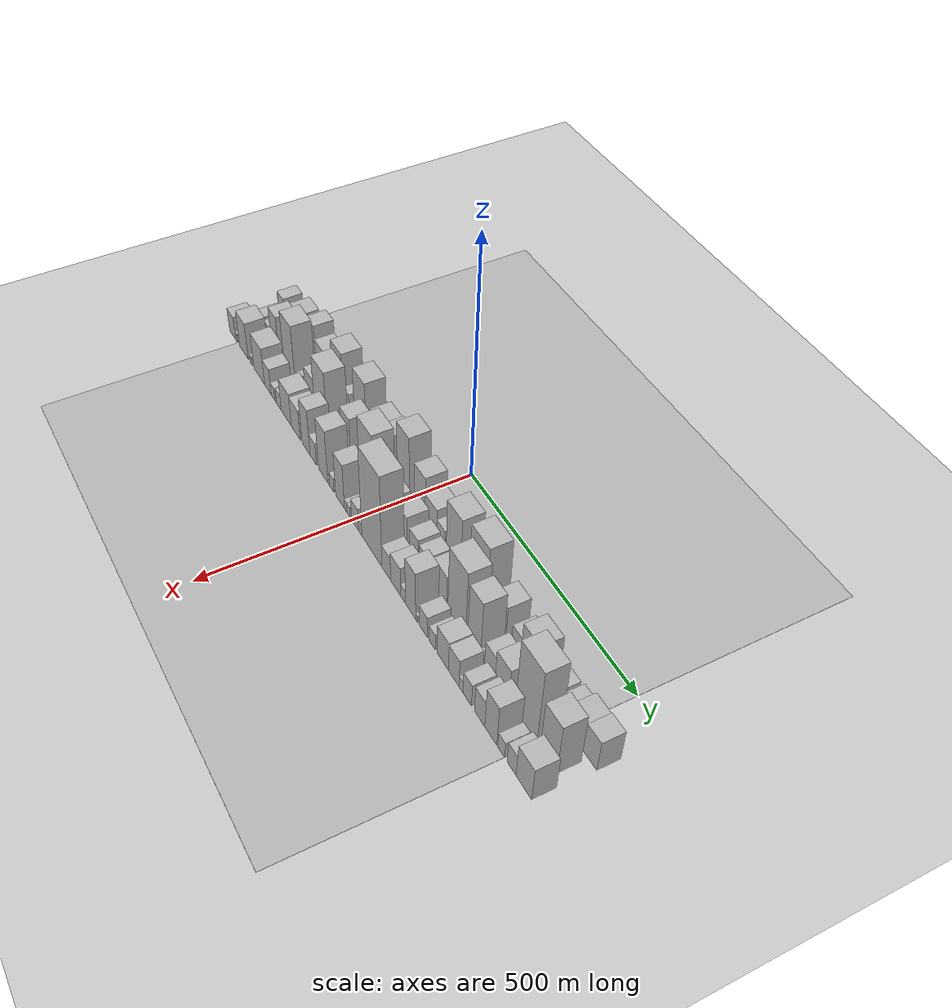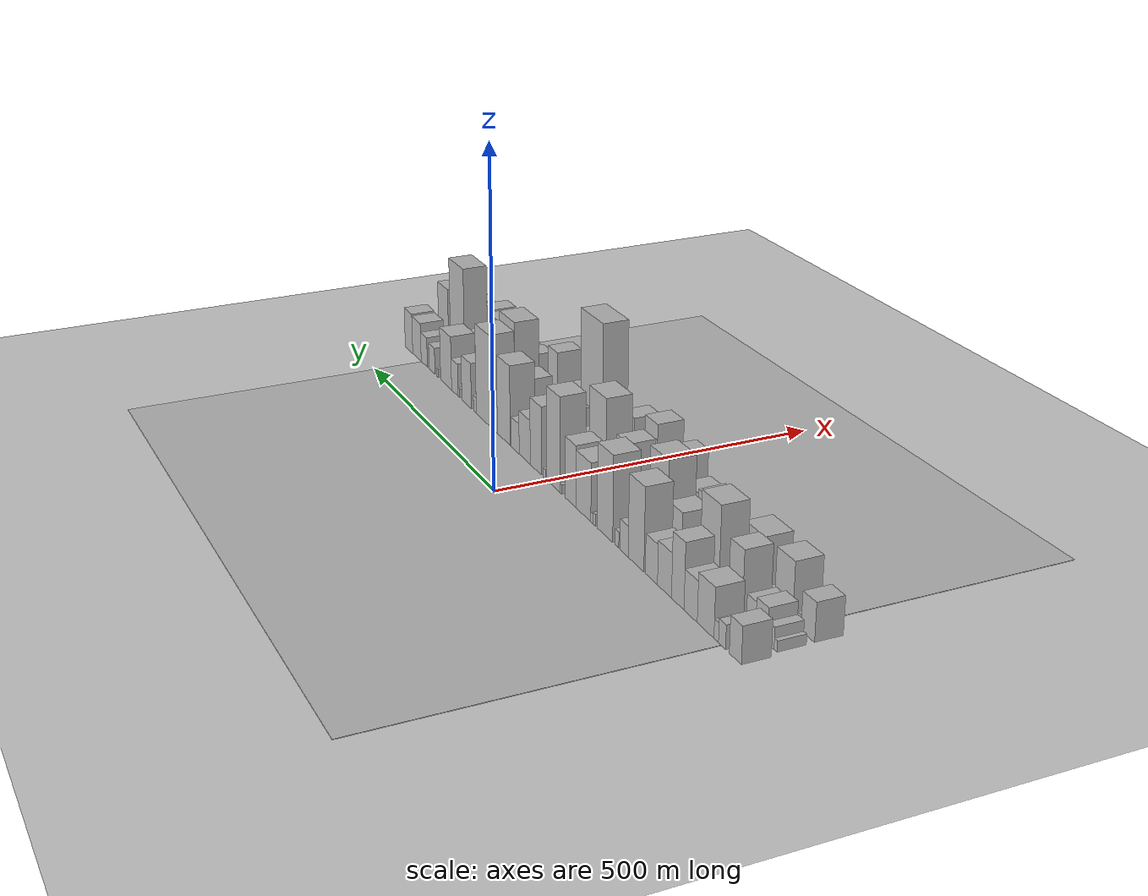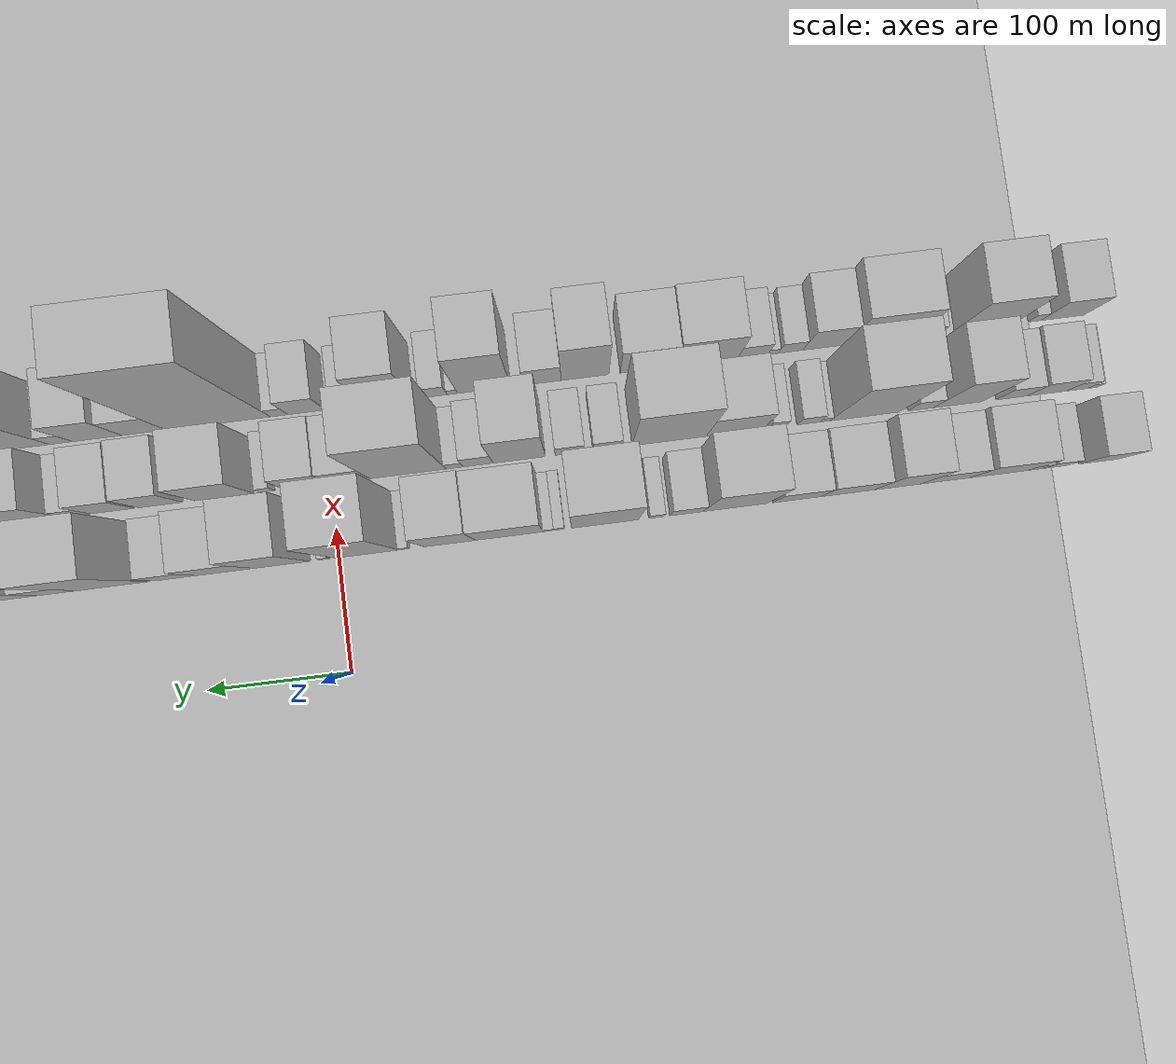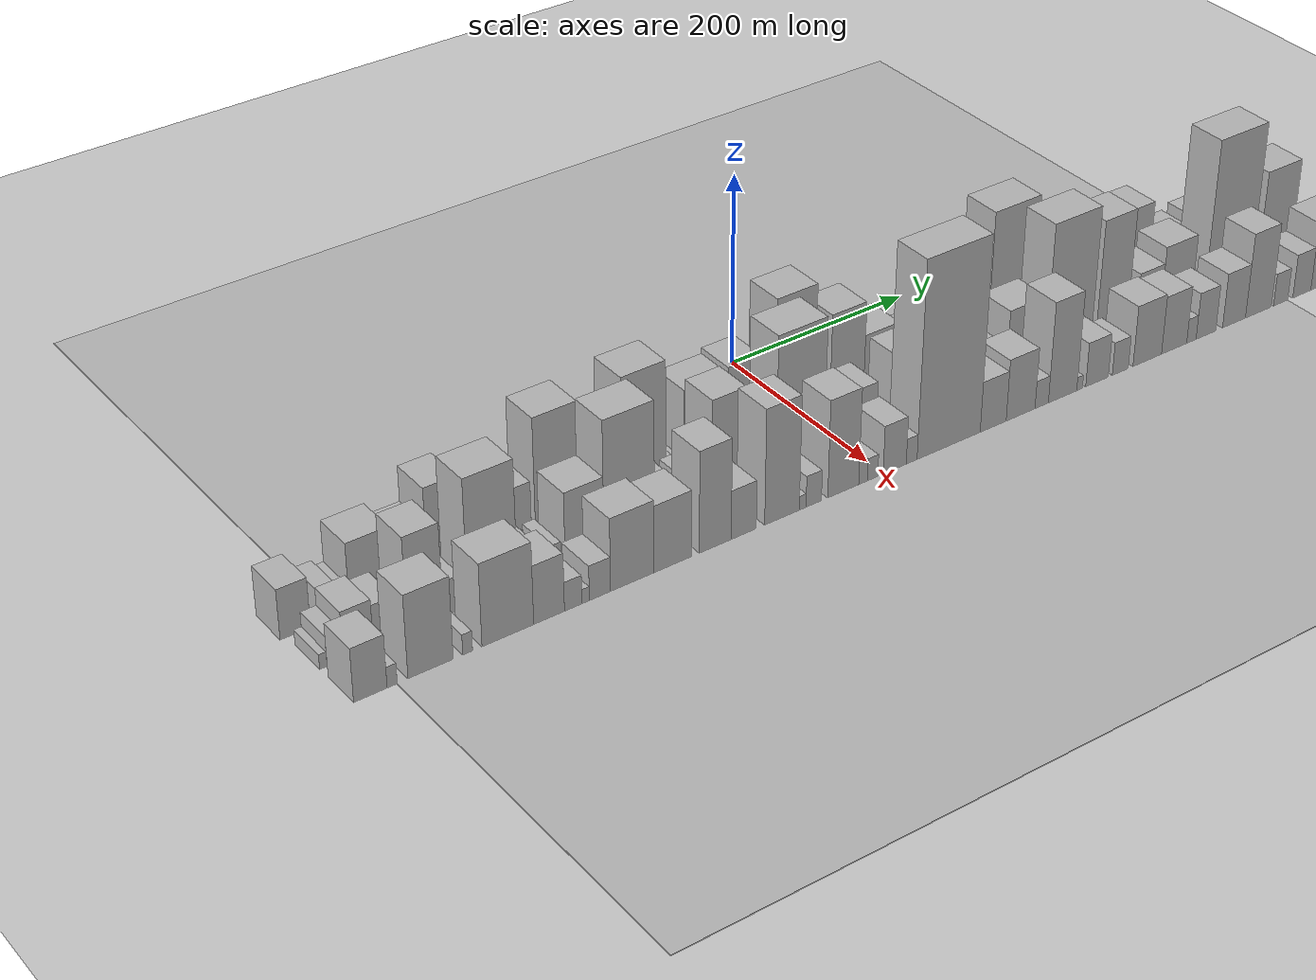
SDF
<?xml version="1.0" encoding="utf-8"?>

<sdf version="1.6">

   <world name="default">

      <gui fullscreen="0">

         <camera name="user_camera">

            <pose>-15 0 4.57585 0 0 0</pose>

            <view_controller>orbit</view_controller>

         </camera>

      </gui>

      <scene>

         <sky>

           <clouds>

             <speed>12</speed>

           </clouds>

         </sky>

         <ambient>0.4 0.4 0.4 1</ambient>

         <background>0.7 0.7 0.7 1</background>

         <shadows>1</shadows>

      </scene>

      <gravity>0 0 -9.8066</gravity>

      <magnetic_field>6e-06 2.3e-05 -4.2e-05</magnetic_field>

      <physics default="0" name="default_physics" type="ode">

         <ode>

            <solver>

               <type>quick</type>

               <iters>10</iters>

               <sor>1.0</sor>

               <use_dynamic_moi_rescaling>0</use_dynamic_moi_rescaling>

            </solver>

            <constraints>

               <cfm>0</cfm>

               <erp>0.2</erp>

               <contact_max_correcting_vel>100</contact_max_correcting_vel>

               <contact_surface_layer>0.001</contact_surface_layer>

            </constraints>

         </ode>

         <max_step_size>0.004</max_step_size>

         <real_time_factor>1</real_time_factor>

         <real_time_update_rate>250</real_time_update_rate>

      </physics>

      <light name="sun" type="directional">

         <cast_shadows>1</cast_shadows>

         <pose>0 0 10 0 0 0</pose>

         <diffuse>0.8 0.8 0.8 1</diffuse>

         <specular>0.2 0.2 0.2 1</specular>

         <attenuation>

            <range>1000</range>

            <constant>0.9</constant>

            <linear>0.01</linear>

            <quadratic>0.001</quadratic>

         </attenuation>

         <direction>-0.5 0.1 -0.9</direction>

      </light>

      <include>

         <name>ground_plane_1</name>

         <uri>model://HANNAS_ground_plane</uri>

         <pose>0 0 0  0 0 0</pose>

      </include>

      <include>

         <name>ground_plane_2</name>

         <uri>model://HANNAS_ground_plane</uri>

         <pose>100 0 0  0 0 0</pose>

      </include>

      <model name="building_1">

         <static>1</static>

         <pose frame="">100.0000 -533.7878 0 0.000000 0.000000 0.000000</pose>

         <link name="link">

            <pose frame="">0 0 25.50 0 0 0</pose>

            <collision name="collision">

               <geometry>

                  <box>

                     <size>40.0000 28.4243 51.0000</size>

                  </box>

               </geometry>

               <max_contacts>10</max_contacts>

               <surface>

                  <contact>

                     <ode/>

                  </contact>

                  <bounce/>

                  <friction>

                     <torsional>

                        <ode/>

                     </torsional>

                     <ode/>

                  </friction>

               </surface>

            </collision>

            <visual name="visual">

               <cast_shadows>0</cast_shadows>

               <geometry>

                  <box>

                     <size>40.0000 28.4243 51.0000</size>

                  </box>

               </geometry>

               <material>

                  <script>

                     <uri>model://HANNAS_wall/materials/scripts</uri>

                     <uri>model://HANNAS_wall/materials/textures</uri>

                     <name>vrc/HANNAS_wall</name>

                  </script>

               </material>

            </visual>

            <self_collide>0</self_collide>

            <enable_wind>0</enable_wind>

            <kinematic>0</kinematic>

         </link>

      </model>

      <model name="building_2">

         <static>1</static>

         <pose frame="">100.0000 -502.0530 0 0.000000 0.000000 0.000000</pose>

         <link name="link">

            <pose frame="">0 0 16.50 0 0 0</pose>

            <collision name="collision">

               <geometry>

                  <box>

                     <size>40.0000 17.0454 33.0000</size>

                  </box>

               </geometry>

               <max_contacts>10</max_contacts>

               <surface>

                  <contact>

                     <ode/>

                  </contact>

                  <bounce/>

                  <friction>

                     <torsional>

                        <ode/>

                     </torsional>

                     <ode/>

                  </friction>

               </surface>

            </collision>

            <visual name="visual">

               <cast_shadows>0</cast_shadows>

               <geometry>

                  <box>

                     <size>40.0000 17.0454 33.0000</size>

                  </box>

               </geometry>

               <material>

                  <script>

                     <uri>model://HANNAS_wall/materials/scripts</uri>

                     <uri>model://HANNAS_wall/materials/textures</uri>

                     <name>vrc/HANNAS_wall</name>

                  </script>

               </material>

            </visual>

            <self_collide>0</self_collide>

            <enable_wind>0</enable_wind>

            <kinematic>0</kinematic>

         </link>

      </model>

      <model name="building_3">

         <static>1</static>

         <pose frame="">100.0000 -487.9994 0 0.000000 0.000000 0.000000</pose>

         <link name="link">

            <pose frame="">0 0 13.50 0 0 0</pose>

            <collision name="collision">

               <geometry>

                  <box>

                     <size>40.0000 11.0617 27.0000</size>

                  </box>

               </geometry>

               <max_contacts>10</max_contacts>

               <surface>

                  <contact>

                     <ode/>

                  </contact>

                  <bounce/>

                  <friction>

                     <torsional>

                        <ode/>

                     </torsional>

                     <ode/>

                  </friction>

               </surface>

            </collision>

            <visual name="visual">

               <cast_shadows>0</cast_shadows>

               <geometry>

                  <box>

                     <size>40.0000 11.0617 27.0000</size>

                  </box>

               </geometry>

               <material>

                  <script>

                     <uri>model://HANNAS_wall/materials/scripts</uri>

                     <uri>model://HANNAS_wall/materials/textures</uri>

                     <name>vrc/HANNAS_wall</name>

                  </script>

               </material>

            </visual>

            <self_collide>0</self_collide>

            <enable_wind>0</enable_wind>

            <kinematic>0</kinematic>

         </link>

      </model>

      <model name="building_4">

         <static>1</static>

         <pose frame="">100.0000 -461.7784 0 0.000000 0.000000 0.000000</pose>

         <link name="link">

            <pose frame="">0 0 34.50 0 0 0</pose>

            <collision name="collision">

               <geometry>

                  <box>

                     <size>40.0000 41.3804 69.0000</size>

                  </box>

               </geometry>

               <max_contacts>10</max_contacts>

               <surface>

                  <contact>

                     <ode/>

                  </contact>

                  <bounce/>

                  <friction>

                     <torsional>

                        <ode/>

                     </torsional>

                     <ode/>

                  </friction>

               </surface>

            </collision>

            <visual name="visual">

               <cast_shadows>0</cast_shadows>

               <geometry>

                  <box>

                     <size>40.0000 41.3804 69.0000</size>

                  </box>

               </geometry>

               <material>

                  <script>

                     <uri>model://HANNAS_wall/materials/scripts</uri>

                     <uri>model://HANNAS_wall/materials/textures</uri>

                     <name>vrc/HANNAS_wall</name>

                  </script>

               </material>

            </visual>

            <self_collide>0</self_collide>

            <enable_wind>0</enable_wind>

            <kinematic>0</kinematic>

         </link>

      </model>

      <model name="building_5">

         <static>1</static>

         <pose frame="">100.0000 -424.1361 0 0.000000 0.000000 0.000000</pose>

         <link name="link">

            <pose frame="">0 0 28.50 0 0 0</pose>

            <collision name="collision">

               <geometry>

                  <box>

                     <size>40.0000 33.9042 57.0000</size>

                  </box>

               </geometry>

               <max_contacts>10</max_contacts>

               <surface>

                  <contact>

                     <ode/>

                  </contact>

                  <bounce/>

                  <friction>

                     <torsional>

                        <ode/>

                     </torsional>

                     <ode/>

                  </friction>

               </surface>

            </collision>

            <visual name="visual">

               <cast_shadows>0</cast_shadows>

               <geometry>

                  <box>

                     <size>40.0000 33.9042 57.0000</size>

                  </box>

               </geometry>

               <material>

                  <script>

                     <uri>model://HANNAS_wall/materials/scripts</uri>

                     <uri>model://HANNAS_wall/materials/textures</uri>

                     <name>vrc/HANNAS_wall</name>

                  </script>

               </material>

            </visual>

            <self_collide>0</self_collide>

            <enable_wind>0</enable_wind>

            <kinematic>0</kinematic>

         </link>

      </model>

      <model name="building_6">

         <static>1</static>

         <pose frame="">100.0000 -390.7886 0 0.000000 0.000000 0.000000</pose>

         <link name="link">

            <pose frame="">0 0 46.50 0 0 0</pose>

            <collision name="collision">

               <geometry>

                  <box>

                     <size>40.0000 32.7908 93.0000</size>

                  </box>

               </geometry>

               <max_contacts>10</max_contacts>

               <surface>

                  <contact>

                     <ode/>

                  </contact>

                  <bounce/>

                  <friction>

                     <torsional>

                        <ode/>

                     </torsional>

                     <ode/>

                  </friction>

               </surface>

            </collision>

            <visual name="visual">

               <cast_shadows>0</cast_shadows>

               <geometry>

                  <box>

                     <size>40.0000 32.7908 93.0000</size>

                  </box>

               </geometry>

               <material>

                  <script>

                     <uri>model://HANNAS_wall/materials/scripts</uri>

                     <uri>model://HANNAS_wall/materials/textures</uri>

                     <name>vrc/HANNAS_wall</name>

                  </script>

               </material>

            </visual>

            <self_collide>0</self_collide>

            <enable_wind>0</enable_wind>

            <kinematic>0</kinematic>

         </link>

      </model>

      <model name="building_7">

         <static>1</static>

         <pose frame="">100.0000 -355.5904 0 0.000000 0.000000 0.000000</pose>

         <link name="link">

            <pose frame="">0 0 31.50 0 0 0</pose>

            <collision name="collision">

               <geometry>

                  <box>

                     <size>40.0000 37.6057 63.0000</size>

                  </box>

               </geometry>

               <max_contacts>10</max_contacts>

               <surface>

                  <contact>

                     <ode/>

                  </contact>

                  <bounce/>

                  <friction>

                     <torsional>

                        <ode/>

                     </torsional>

                     <ode/>

                  </friction>

               </surface>

            </collision>

            <visual name="visual">

               <cast_shadows>0</cast_shadows>

               <geometry>

                  <box>

                     <size>40.0000 37.6057 63.0000</size>

                  </box>

               </geometry>

               <material>

                  <script>

                     <uri>model://HANNAS_wall/materials/scripts</uri>

                     <uri>model://HANNAS_wall/materials/textures</uri>

                     <name>vrc/HANNAS_wall</name>

                  </script>

               </material>

            </visual>

            <self_collide>0</self_collide>

            <enable_wind>0</enable_wind>

            <kinematic>0</kinematic>

         </link>

      </model>

      <model name="building_8">

         <static>1</static>

         <pose frame="">100.0000 -319.9944 0 0.000000 0.000000 0.000000</pose>

         <link name="link">

            <pose frame="">0 0 28.50 0 0 0</pose>

            <collision name="collision">

               <geometry>

                  <box>

                     <size>40.0000 33.5863 57.0000</size>

                  </box>

               </geometry>

               <max_contacts>10</max_contacts>

               <surface>

                  <contact>

                     <ode/>

                  </contact>

                  <bounce/>

                  <friction>

                     <torsional>

                        <ode/>

                     </torsional>

                     <ode/>

                  </friction>

               </surface>

            </collision>

            <visual name="visual">

               <cast_shadows>0</cast_shadows>

               <geometry>

                  <box>

                     <size>40.0000 33.5863 57.0000</size>

                  </box>

               </geometry>

               <material>

                  <script>

                     <uri>model://HANNAS_wall/materials/scripts</uri>

                     <uri>model://HANNAS_wall/materials/textures</uri>

                     <name>vrc/HANNAS_wall</name>

                  </script>

               </material>

            </visual>

            <self_collide>0</self_collide>

            <enable_wind>0</enable_wind>

            <kinematic>0</kinematic>

         </link>

      </model>

      <model name="building_9">

         <static>1</static>

         <pose frame="">100.0000 -276.8330 0 0.000000 0.000000 0.000000</pose>

         <link name="link">

            <pose frame="">0 0 60.00 0 0 0</pose>

            <collision name="collision">

               <geometry>

                  <box>

                     <size>40.0000 44.7365 120.0000</size>

                  </box>

               </geometry>

               <max_contacts>10</max_contacts>

               <surface>

                  <contact>

                     <ode/>

                  </contact>

                  <bounce/>

                  <friction>

                     <torsional>

                        <ode/>

                     </torsional>

                     <ode/>

                  </friction>

               </surface>

            </collision>

            <visual name="visual">

               <cast_shadows>0</cast_shadows>

               <geometry>

                  <box>

                     <size>40.0000 44.7365 120.0000</size>

                  </box>

               </geometry>

               <material>

                  <script>

                     <uri>model://HANNAS_wall/materials/scripts</uri>

                     <uri>model://HANNAS_wall/materials/textures</uri>

                     <name>vrc/HANNAS_wall</name>

                  </script>

               </material>

            </visual>

            <self_collide>0</self_collide>

            <enable_wind>0</enable_wind>

            <kinematic>0</kinematic>

         </link>

      </model>

      <model name="building_10">

         <static>1</static>

         <pose frame="">100.0000 -242.7322 0 0.000000 0.000000 0.000000</pose>

         <link name="link">

            <pose frame="">0 0 22.50 0 0 0</pose>

            <collision name="collision">

               <geometry>

                  <box>

                     <size>40.0000 23.4651 45.0000</size>

                  </box>

               </geometry>

               <max_contacts>10</max_contacts>

               <surface>

                  <contact>

                     <ode/>

                  </contact>

                  <bounce/>

                  <friction>

                     <torsional>

                        <ode/>

                     </torsional>

                     <ode/>

                  </friction>

               </surface>

            </collision>

            <visual name="visual">

               <cast_shadows>0</cast_shadows>

               <geometry>

                  <box>

                     <size>40.0000 23.4651 45.0000</size>

                  </box>

               </geometry>

               <material>

                  <script>

                     <uri>model://HANNAS_wall/materials/scripts</uri>

                     <uri>model://HANNAS_wall/materials/textures</uri>

                     <name>vrc/HANNAS_wall</name>

                  </script>

               </material>

            </visual>

            <self_collide>0</self_collide>

            <enable_wind>0</enable_wind>

            <kinematic>0</kinematic>

         </link>

      </model>

      <model name="building_11">

         <static>1</static>

         <pose frame="">100.0000 -221.5795 0 0.000000 0.000000 0.000000</pose>

         <link name="link">

            <pose frame="">0 0 12.00 0 0 0</pose>

            <collision name="collision">

               <geometry>

                  <box>

                     <size>40.0000 10.8404 24.0000</size>

                  </box>

               </geometry>

               <max_contacts>10</max_contacts>

               <surface>

                  <contact>

                     <ode/>

                  </contact>

                  <bounce/>

                  <friction>

                     <torsional>

                        <ode/>

                     </torsional>

                     <ode/>

                  </friction>

               </surface>

            </collision>

            <visual name="visual">

               <cast_shadows>0</cast_shadows>

               <geometry>

                  <box>

                     <size>40.0000 10.8404 24.0000</size>

                  </box>

               </geometry>

               <material>

                  <script>

                     <uri>model://HANNAS_wall/materials/scripts</uri>

                     <uri>model://HANNAS_wall/materials/textures</uri>

                     <name>vrc/HANNAS_wall</name>

                  </script>

               </material>

            </visual>

            <self_collide>0</self_collide>

            <enable_wind>0</enable_wind>

            <kinematic>0</kinematic>

         </link>

      </model>

      <model name="building_12">

         <static>1</static>

         <pose frame="">100.0000 -185.7184 0 0.000000 0.000000 0.000000</pose>

         <link name="link">

            <pose frame="">0 0 63.00 0 0 0</pose>

            <collision name="collision">

               <geometry>

                  <box>

                     <size>40.0000 46.8817 126.0000</size>

                  </box>

               </geometry>

               <max_contacts>10</max_contacts>

               <surface>

                  <contact>

                     <ode/>

                  </contact>

                  <bounce/>

                  <friction>

                     <torsional>

                        <ode/>

                     </torsional>

                     <ode/>

                  </friction>

               </surface>

            </collision>

            <visual name="visual">

               <cast_shadows>0</cast_shadows>

               <geometry>

                  <box>

                     <size>40.0000 46.8817 126.0000</size>

                  </box>

               </geometry>

               <material>

                  <script>

                     <uri>model://HANNAS_wall/materials/scripts</uri>

                     <uri>model://HANNAS_wall/materials/textures</uri>

                     <name>vrc/HANNAS_wall</name>

                  </script>

               </material>

            </visual>

            <self_collide>0</self_collide>

            <enable_wind>0</enable_wind>

            <kinematic>0</kinematic>

         </link>

      </model>

      <model name="building_13">

         <static>1</static>

         <pose frame="">100.0000 -153.5307 0 0.000000 0.000000 0.000000</pose>

         <link name="link">

            <pose frame="">0 0 9.00 0 0 0</pose>

            <collision name="collision">

               <geometry>

                  <box>

                     <size>40.0000 7.4938 18.0000</size>

                  </box>

               </geometry>

               <max_contacts>10</max_contacts>

               <surface>

                  <contact>

                     <ode/>

                  </contact>

                  <bounce/>

                  <friction>

                     <torsional>

                        <ode/>

                     </torsional>

                     <ode/>

                  </friction>

               </surface>

            </collision>

            <visual name="visual">

               <cast_shadows>0</cast_shadows>

               <geometry>

                  <box>

                     <size>40.0000 7.4938 18.0000</size>

                  </box>

               </geometry>

               <material>

                  <script>

                     <uri>model://HANNAS_wall/materials/scripts</uri>

                     <uri>model://HANNAS_wall/materials/textures</uri>

                     <name>vrc/HANNAS_wall</name>

                  </script>

               </material>

            </visual>

            <self_collide>0</self_collide>

            <enable_wind>0</enable_wind>

            <kinematic>0</kinematic>

         </link>

      </model>

      <model name="building_14">

         <static>1</static>

         <pose frame="">100.0000 -146.0817 0 0.000000 0.000000 0.000000</pose>

         <link name="link">

            <pose frame="">0 0 7.50 0 0 0</pose>

            <collision name="collision">

               <geometry>

                  <box>

                     <size>40.0000 7.4043 15.0000</size>

                  </box>

               </geometry>

               <max_contacts>10</max_contacts>

               <surface>

                  <contact>

                     <ode/>

                  </contact>

                  <bounce/>

                  <friction>

                     <torsional>

                        <ode/>

                     </torsional>

                     <ode/>

                  </friction>

               </surface>

            </collision>

            <visual name="visual">

               <cast_shadows>0</cast_shadows>

               <geometry>

                  <box>

                     <size>40.0000 7.4043 15.0000</size>

                  </box>

               </geometry>

               <material>

                  <script>

                     <uri>model://HANNAS_wall/materials/scripts</uri>

                     <uri>model://HANNAS_wall/materials/textures</uri>

                     <name>vrc/HANNAS_wall</name>

                  </script>

               </material>

            </visual>

            <self_collide>0</self_collide>

            <enable_wind>0</enable_wind>

            <kinematic>0</kinematic>

         </link>

      </model>

      <model name="building_15">

         <static>1</static>

         <pose frame="">100.0000 -118.7138 0 0.000000 0.000000 0.000000</pose>

         <link name="link">

            <pose frame="">0 0 43.50 0 0 0</pose>

            <collision name="collision">

               <geometry>

                  <box>

                     <size>40.0000 47.3314 87.0000</size>

                  </box>

               </geometry>

               <max_contacts>10</max_contacts>

               <surface>

                  <contact>

                     <ode/>

                  </contact>

                  <bounce/>

                  <friction>

                     <torsional>

                        <ode/>

                     </torsional>

                     <ode/>

                  </friction>

               </surface>

            </collision>

            <visual name="visual">

               <cast_shadows>0</cast_shadows>

               <geometry>

                  <box>

                     <size>40.0000 47.3314 87.0000</size>

                  </box>

               </geometry>

               <material>

                  <script>

                     <uri>model://HANNAS_wall/materials/scripts</uri>

                     <uri>model://HANNAS_wall/materials/textures</uri>

                     <name>vrc/HANNAS_wall</name>

                  </script>

               </material>

            </visual>

            <self_collide>0</self_collide>

            <enable_wind>0</enable_wind>

            <kinematic>0</kinematic>

         </link>

      </model>

      <model name="building_16">

         <static>1</static>

         <pose frame="">100.0000 -77.1451 0 0.000000 0.000000 0.000000</pose>

         <link name="link">

            <pose frame="">0 0 46.50 0 0 0</pose>

            <collision name="collision">

               <geometry>

                  <box>

                     <size>40.0000 35.8060 93.0000</size>

                  </box>

               </geometry>

               <max_contacts>10</max_contacts>

               <surface>

                  <contact>

                     <ode/>

                  </contact>

                  <bounce/>

                  <friction>

                     <torsional>

                        <ode/>

                     </torsional>

                     <ode/>

                  </friction>

               </surface>

            </collision>

            <visual name="visual">

               <cast_shadows>0</cast_shadows>

               <geometry>

                  <box>

                     <size>40.0000 35.8060 93.0000</size>

                  </box>

               </geometry>

               <material>

                  <script>

                     <uri>model://HANNAS_wall/materials/scripts</uri>

                     <uri>model://HANNAS_wall/materials/textures</uri>

                     <name>vrc/HANNAS_wall</name>

                  </script>

               </material>

            </visual>

            <self_collide>0</self_collide>

            <enable_wind>0</enable_wind>

            <kinematic>0</kinematic>

         </link>

      </model>

      <model name="building_17">

         <static>1</static>

         <pose frame="">100.0000 -45.6650 0 0.000000 0.000000 0.000000</pose>

         <link name="link">

            <pose frame="">0 0 7.50 0 0 0</pose>

            <collision name="collision">

               <geometry>

                  <box>

                     <size>40.0000 7.1542 15.0000</size>

                  </box>

               </geometry>

               <max_contacts>10</max_contacts>

               <surface>

                  <contact>

                     <ode/>

                  </contact>

                  <bounce/>

                  <friction>

                     <torsional>

                        <ode/>

                     </torsional>

                     <ode/>

                  </friction>

               </surface>

            </collision>

            <visual name="visual">

               <cast_shadows>0</cast_shadows>

               <geometry>

                  <box>

                     <size>40.0000 7.1542 15.0000</size>

                  </box>

               </geometry>

               <material>

                  <script>

                     <uri>model://HANNAS_wall/materials/scripts</uri>

                     <uri>model://HANNAS_wall/materials/textures</uri>

                     <name>vrc/HANNAS_wall</name>

                  </script>

               </material>

            </visual>

            <self_collide>0</self_collide>

            <enable_wind>0</enable_wind>

            <kinematic>0</kinematic>

         </link>

      </model>

      <model name="building_18">

         <static>1</static>

         <pose frame="">100.0000 -19.7245 0 0.000000 0.000000 0.000000</pose>

         <link name="link">

            <pose frame="">0 0 72.00 0 0 0</pose>

            <collision name="collision">

               <geometry>

                  <box>

                     <size>40.0000 44.7270 144.0000</size>

                  </box>

               </geometry>

               <max_contacts>10</max_contacts>

               <surface>

                  <contact>

                     <ode/>

                  </contact>

                  <bounce/>

                  <friction>

                     <torsional>

                        <ode/>

                     </torsional>

                     <ode/>

                  </friction>

               </surface>

            </collision>

            <visual name="visual">

               <cast_shadows>0</cast_shadows>

               <geometry>

                  <box>

                     <size>40.0000 44.7270 144.0000</size>

                  </box>

               </geometry>

               <material>

                  <script>

                     <uri>model://HANNAS_wall/materials/scripts</uri>

                     <uri>model://HANNAS_wall/materials/textures</uri>

                     <name>vrc/HANNAS_wall</name>

                  </script>

               </material>

            </visual>

            <self_collide>0</self_collide>

            <enable_wind>0</enable_wind>

            <kinematic>0</kinematic>

         </link>

      </model>

      <model name="building_19">

         <static>1</static>

         <pose frame="">100.0000 9.9743 0 0.000000 0.000000 0.000000</pose>

         <link name="link">

            <pose frame="">0 0 7.50 0 0 0</pose>

            <collision name="collision">

               <geometry>

                  <box>

                     <size>40.0000 6.6705 15.0000</size>

                  </box>

               </geometry>

               <max_contacts>10</max_contacts>

               <surface>

                  <contact>

                     <ode/>

                  </contact>

                  <bounce/>

                  <friction>

                     <torsional>

                        <ode/>

                     </torsional>

                     <ode/>

                  </friction>

               </surface>

            </collision>

            <visual name="visual">

               <cast_shadows>0</cast_shadows>

               <geometry>

                  <box>

                     <size>40.0000 6.6705 15.0000</size>

                  </box>

               </geometry>

               <material>

                  <script>

                     <uri>model://HANNAS_wall/materials/scripts</uri>

                     <uri>model://HANNAS_wall/materials/textures</uri>

                     <name>vrc/HANNAS_wall</name>

                  </script>

               </material>

            </visual>

            <self_collide>0</self_collide>

            <enable_wind>0</enable_wind>

            <kinematic>0</kinematic>

         </link>

      </model>

      <model name="building_20">

         <static>1</static>

         <pose frame="">100.0000 39.8482 0 0.000000 0.000000 0.000000</pose>

         <link name="link">

            <pose frame="">0 0 52.50 0 0 0</pose>

            <collision name="collision">

               <geometry>

                  <box>

                     <size>40.0000 39.0774 105.0000</size>

                  </box>

               </geometry>

               <max_contacts>10</max_contacts>

               <surface>

                  <contact>

                     <ode/>

                  </contact>

                  <bounce/>

                  <friction>

                     <torsional>

                        <ode/>

                     </torsional>

                     <ode/>

                  </friction>

               </surface>

            </collision>

            <visual name="visual">

               <cast_shadows>0</cast_shadows>

               <geometry>

                  <box>

                     <size>40.0000 39.0774 105.0000</size>

                  </box>

               </geometry>

               <material>

                  <script>

                     <uri>model://HANNAS_wall/materials/scripts</uri>

                     <uri>model://HANNAS_wall/materials/textures</uri>

                     <name>vrc/HANNAS_wall</name>

                  </script>

               </material>

            </visual>

            <self_collide>0</self_collide>

            <enable_wind>0</enable_wind>

            <kinematic>0</kinematic>

         </link>

      </model>

      <model name="building_21">

         <static>1</static>

         <pose frame="">100.0000 79.3136 0 0.000000 0.000000 0.000000</pose>

         <link name="link">

            <pose frame="">0 0 34.50 0 0 0</pose>

            <collision name="collision">

               <geometry>

                  <box>

                     <size>40.0000 39.8534 69.0000</size>

                  </box>

               </geometry>

               <max_contacts>10</max_contacts>

               <surface>

                  <contact>

                     <ode/>

                  </contact>

                  <bounce/>

                  <friction>

                     <torsional>

                        <ode/>

                     </torsional>

                     <ode/>

                  </friction>

               </surface>

            </collision>

            <visual name="visual">

               <cast_shadows>0</cast_shadows>

               <geometry>

                  <box>

                     <size>40.0000 39.8534 69.0000</size>

                  </box>

               </geometry>

               <material>

                  <script>

                     <uri>model://HANNAS_wall/materials/scripts</uri>

                     <uri>model://HANNAS_wall/materials/textures</uri>

                     <name>vrc/HANNAS_wall</name>

                  </script>

               </material>

            </visual>

            <self_collide>0</self_collide>

            <enable_wind>0</enable_wind>

            <kinematic>0</kinematic>

         </link>

      </model>

      <model name="building_22">

         <static>1</static>

         <pose frame="">100.0000 113.6267 0 0.000000 0.000000 0.000000</pose>

         <link name="link">

            <pose frame="">0 0 24.00 0 0 0</pose>

            <collision name="collision">

               <geometry>

                  <box>

                     <size>40.0000 28.7727 48.0000</size>

                  </box>

               </geometry>

               <max_contacts>10</max_contacts>

               <surface>

                  <contact>

                     <ode/>

                  </contact>

                  <bounce/>

                  <friction>

                     <torsional>

                        <ode/>

                     </torsional>

                     <ode/>

                  </friction>

               </surface>

            </collision>

            <visual name="visual">

               <cast_shadows>0</cast_shadows>

               <geometry>

                  <box>

                     <size>40.0000 28.7727 48.0000</size>

                  </box>

               </geometry>

               <material>

                  <script>

                     <uri>model://HANNAS_wall/materials/scripts</uri>

                     <uri>model://HANNAS_wall/materials/textures</uri>

                     <name>vrc/HANNAS_wall</name>

                  </script>

               </material>

            </visual>

            <self_collide>0</self_collide>

            <enable_wind>0</enable_wind>

            <kinematic>0</kinematic>

         </link>

      </model>

      <model name="building_23">

         <static>1</static>

         <pose frame="">100.0000 156.3978 0 0.000000 0.000000 0.000000</pose>

         <link name="link">

            <pose frame="">0 0 63.00 0 0 0</pose>

            <collision name="collision">

               <geometry>

                  <box>

                     <size>40.0000 48.7695 126.0000</size>

                  </box>

               </geometry>

               <max_contacts>10</max_contacts>

               <surface>

                  <contact>

                     <ode/>

                  </contact>

                  <bounce/>

                  <friction>

                     <torsional>

                        <ode/>

                     </torsional>

                     <ode/>

                  </friction>

               </surface>

            </collision>

            <visual name="visual">

               <cast_shadows>0</cast_shadows>

               <geometry>

                  <box>

                     <size>40.0000 48.7695 126.0000</size>

                  </box>

               </geometry>

               <material>

                  <script>

                     <uri>model://HANNAS_wall/materials/scripts</uri>

                     <uri>model://HANNAS_wall/materials/textures</uri>

                     <name>vrc/HANNAS_wall</name>

                  </script>

               </material>

            </visual>

            <self_collide>0</self_collide>

            <enable_wind>0</enable_wind>

            <kinematic>0</kinematic>

         </link>

      </model>

      <model name="building_24">

         <static>1</static>

         <pose frame="">100.0000 194.5604 0 0.000000 0.000000 0.000000</pose>

         <link name="link">

            <pose frame="">0 0 27.00 0 0 0</pose>

            <collision name="collision">

               <geometry>

                  <box>

                     <size>40.0000 27.5558 54.0000</size>

                  </box>

               </geometry>

               <max_contacts>10</max_contacts>

               <surface>

                  <contact>

                     <ode/>

                  </contact>

                  <bounce/>

                  <friction>

                     <torsional>

                        <ode/>

                     </torsional>

                     <ode/>

                  </friction>

               </surface>

            </collision>

            <visual name="visual">

               <cast_shadows>0</cast_shadows>

               <geometry>

                  <box>

                     <size>40.0000 27.5558 54.0000</size>

                  </box>

               </geometry>

               <material>

                  <script>

                     <uri>model://HANNAS_wall/materials/scripts</uri>

                     <uri>model://HANNAS_wall/materials/textures</uri>

                     <name>vrc/HANNAS_wall</name>

                  </script>

               </material>

            </visual>

            <self_collide>0</self_collide>

            <enable_wind>0</enable_wind>

            <kinematic>0</kinematic>

         </link>

      </model>

      <model name="building_25">

         <static>1</static>

         <pose frame="">100.0000 236.0614 0 0.000000 0.000000 0.000000</pose>

         <link name="link">

            <pose frame="">0 0 73.50 0 0 0</pose>

            <collision name="collision">

               <geometry>

                  <box>

                     <size>40.0000 55.4461 147.0000</size>

                  </box>

               </geometry>

               <max_contacts>10</max_contacts>

               <surface>

                  <contact>

                     <ode/>

                  </contact>

                  <bounce/>

                  <friction>

                     <torsional>

                        <ode/>

                     </torsional>

                     <ode/>

                  </friction>

               </surface>

            </collision>

            <visual name="visual">

               <cast_shadows>0</cast_shadows>

               <geometry>

                  <box>

                     <size>40.0000 55.4461 147.0000</size>

                  </box>

               </geometry>

               <material>

                  <script>

                     <uri>model://HANNAS_wall/materials/scripts</uri>

                     <uri>model://HANNAS_wall/materials/textures</uri>

                     <name>vrc/HANNAS_wall</name>

                  </script>

               </material>

            </visual>

            <self_collide>0</self_collide>

            <enable_wind>0</enable_wind>

            <kinematic>0</kinematic>

         </link>

      </model>

      <model name="building_26">

         <static>1</static>

         <pose frame="">100.0000 269.3358 0 0.000000 0.000000 0.000000</pose>

         <link name="link">

            <pose frame="">0 0 13.50 0 0 0</pose>

            <collision name="collision">

               <geometry>

                  <box>

                     <size>40.0000 11.1029 27.0000</size>

                  </box>

               </geometry>

               <max_contacts>10</max_contacts>

               <surface>

                  <contact>

                     <ode/>

                  </contact>

                  <bounce/>

                  <friction>

                     <torsional>

                        <ode/>

                     </torsional>

                     <ode/>

                  </friction>

               </surface>

            </collision>

            <visual name="visual">

               <cast_shadows>0</cast_shadows>

               <geometry>

                  <box>

                     <size>40.0000 11.1029 27.0000</size>

                  </box>

               </geometry>

               <material>

                  <script>

                     <uri>model://HANNAS_wall/materials/scripts</uri>

                     <uri>model://HANNAS_wall/materials/textures</uri>

                     <name>vrc/HANNAS_wall</name>

                  </script>

               </material>

            </visual>

            <self_collide>0</self_collide>

            <enable_wind>0</enable_wind>

            <kinematic>0</kinematic>

         </link>

      </model>

      <model name="building_27">

         <static>1</static>

         <pose frame="">100.0000 303.4332 0 0.000000 0.000000 0.000000</pose>

         <link name="link">

            <pose frame="">0 0 37.50 0 0 0</pose>

            <collision name="collision">

               <geometry>

                  <box>

                     <size>40.0000 39.0918 75.0000</size>

                  </box>

               </geometry>

               <max_contacts>10</max_contacts>

               <surface>

                  <contact>

                     <ode/>

                  </contact>

                  <bounce/>

                  <friction>

                     <torsional>

                        <ode/>

                     </torsional>

                     <ode/>

                  </friction>

               </surface>

            </collision>

            <visual name="visual">

               <cast_shadows>0</cast_shadows>

               <geometry>

                  <box>

                     <size>40.0000 39.0918 75.0000</size>

                  </box>

               </geometry>

               <material>

                  <script>

                     <uri>model://HANNAS_wall/materials/scripts</uri>

                     <uri>model://HANNAS_wall/materials/textures</uri>

                     <name>vrc/HANNAS_wall</name>

                  </script>

               </material>

            </visual>

            <self_collide>0</self_collide>

            <enable_wind>0</enable_wind>

            <kinematic>0</kinematic>

         </link>

      </model>

      <model name="building_28">

         <static>1</static>

         <pose frame="">100.0000 335.3981 0 0.000000 0.000000 0.000000</pose>

         <link name="link">

            <pose frame="">0 0 7.50 0 0 0</pose>

            <collision name="collision">

               <geometry>

                  <box>

                     <size>40.0000 6.8379 15.0000</size>

                  </box>

               </geometry>

               <max_contacts>10</max_contacts>

               <surface>

                  <contact>

                     <ode/>

                  </contact>

                  <bounce/>

                  <friction>

                     <torsional>

                        <ode/>

                     </torsional>

                     <ode/>

                  </friction>

               </surface>

            </collision>

            <visual name="visual">

               <cast_shadows>0</cast_shadows>

               <geometry>

                  <box>

                     <size>40.0000 6.8379 15.0000</size>

                  </box>

               </geometry>

               <material>

                  <script>

                     <uri>model://HANNAS_wall/materials/scripts</uri>

                     <uri>model://HANNAS_wall/materials/textures</uri>

                     <name>vrc/HANNAS_wall</name>

                  </script>

               </material>

            </visual>

            <self_collide>0</self_collide>

            <enable_wind>0</enable_wind>

            <kinematic>0</kinematic>

         </link>

      </model>

      <model name="building_29">

         <static>1</static>

         <pose frame="">100.0000 352.5228 0 0.000000 0.000000 0.000000</pose>

         <link name="link">

            <pose frame="">0 0 27.00 0 0 0</pose>

            <collision name="collision">

               <geometry>

                  <box>

                     <size>40.0000 27.4115 54.0000</size>

                  </box>

               </geometry>

               <max_contacts>10</max_contacts>

               <surface>

                  <contact>

                     <ode/>

                  </contact>

                  <bounce/>

                  <friction>

                     <torsional>

                        <ode/>

                     </torsional>

                     <ode/>

                  </friction>

               </surface>

            </collision>

            <visual name="visual">

               <cast_shadows>0</cast_shadows>

               <geometry>

                  <box>

                     <size>40.0000 27.4115 54.0000</size>

                  </box>

               </geometry>

               <material>

                  <script>

                     <uri>model://HANNAS_wall/materials/scripts</uri>

                     <uri>model://HANNAS_wall/materials/textures</uri>

                     <name>vrc/HANNAS_wall</name>

                  </script>

               </material>

            </visual>

            <self_collide>0</self_collide>

            <enable_wind>0</enable_wind>

            <kinematic>0</kinematic>

         </link>

      </model>

      <model name="building_30">

         <static>1</static>

         <pose frame="">100.0000 389.9765 0 0.000000 0.000000 0.000000</pose>

         <link name="link">

            <pose frame="">0 0 45.00 0 0 0</pose>

            <collision name="collision">

               <geometry>

                  <box>

                     <size>40.0000 47.4959 90.0000</size>

                  </box>

               </geometry>

               <max_contacts>10</max_contacts>

               <surface>

                  <contact>

                     <ode/>

                  </contact>

                  <bounce/>

                  <friction>

                     <torsional>

                        <ode/>

                     </torsional>

                     <ode/>

                  </friction>

               </surface>

            </collision>

            <visual name="visual">

               <cast_shadows>0</cast_shadows>

               <geometry>

                  <box>

                     <size>40.0000 47.4959 90.0000</size>

                  </box>

               </geometry>

               <material>

                  <script>

                     <uri>model://HANNAS_wall/materials/scripts</uri>

                     <uri>model://HANNAS_wall/materials/textures</uri>

                     <name>vrc/HANNAS_wall</name>

                  </script>

               </material>

            </visual>

            <self_collide>0</self_collide>

            <enable_wind>0</enable_wind>

            <kinematic>0</kinematic>

         </link>

      </model>

      <model name="building_31">

         <static>1</static>

         <pose frame="">100.0000 426.9344 0 0.000000 0.000000 0.000000</pose>

         <link name="link">

            <pose frame="">0 0 7.50 0 0 0</pose>

            <collision name="collision">

               <geometry>

                  <box>

                     <size>40.0000 6.4199 15.0000</size>

                  </box>

               </geometry>

               <max_contacts>10</max_contacts>

               <surface>

                  <contact>

                     <ode/>

                  </contact>

                  <bounce/>

                  <friction>

                     <torsional>

                        <ode/>

                     </torsional>

                     <ode/>

                  </friction>

               </surface>

            </collision>

            <visual name="visual">

               <cast_shadows>0</cast_shadows>

               <geometry>

                  <box>

                     <size>40.0000 6.4199 15.0000</size>

                  </box>

               </geometry>

               <material>

                  <script>

                     <uri>model://HANNAS_wall/materials/scripts</uri>

                     <uri>model://HANNAS_wall/materials/textures</uri>

                     <name>vrc/HANNAS_wall</name>

                  </script>

               </material>

            </visual>

            <self_collide>0</self_collide>

            <enable_wind>0</enable_wind>

            <kinematic>0</kinematic>

         </link>

      </model>

      <model name="building_32">

         <static>1</static>

         <pose frame="">100.0000 452.2859 0 0.000000 0.000000 0.000000</pose>

         <link name="link">

            <pose frame="">0 0 22.50 0 0 0</pose>

            <collision name="collision">

               <geometry>

                  <box>

                     <size>40.0000 26.2831 45.0000</size>

                  </box>

               </geometry>

               <max_contacts>10</max_contacts>

               <surface>

                  <contact>

                     <ode/>

                  </contact>

                  <bounce/>

                  <friction>

                     <torsional>

                        <ode/>

                     </torsional>

                     <ode/>

                  </friction>

               </surface>

            </collision>

            <visual name="visual">

               <cast_shadows>0</cast_shadows>

               <geometry>

                  <box>

                     <size>40.0000 26.2831 45.0000</size>

                  </box>

               </geometry>

               <material>

                  <script>

                     <uri>model://HANNAS_wall/materials/scripts</uri>

                     <uri>model://HANNAS_wall/materials/textures</uri>

                     <name>vrc/HANNAS_wall</name>

                  </script>

               </material>

            </visual>

            <self_collide>0</self_collide>

            <enable_wind>0</enable_wind>

            <kinematic>0</kinematic>

         </link>

      </model>

      <model name="building_33">

         <static>1</static>

         <pose frame="">100.0000 487.6147 0 0.000000 0.000000 0.000000</pose>

         <link name="link">

            <pose frame="">0 0 25.50 0 0 0</pose>

            <collision name="collision">

               <geometry>

                  <box>

                     <size>40.0000 28.3746 51.0000</size>

                  </box>

               </geometry>

               <max_contacts>10</max_contacts>

               <surface>

                  <contact>

                     <ode/>

                  </contact>

                  <bounce/>

                  <friction>

                     <torsional>

                        <ode/>

                     </torsional>

                     <ode/>

                  </friction>

               </surface>

            </collision>

            <visual name="visual">

               <cast_shadows>0</cast_shadows>

               <geometry>

                  <box>

                     <size>40.0000 28.3746 51.0000</size>

                  </box>

               </geometry>

               <material>

                  <script>

                     <uri>model://HANNAS_wall/materials/scripts</uri>

                     <uri>model://HANNAS_wall/materials/textures</uri>

                     <name>vrc/HANNAS_wall</name>

                  </script>

               </material>

            </visual>

            <self_collide>0</self_collide>

            <enable_wind>0</enable_wind>

            <kinematic>0</kinematic>

         </link>

      </model>

      <model name="building_34">

         <static>1</static>

         <pose frame="">100.0000 521.4848 0 0.000000 0.000000 0.000000</pose>

         <link name="link">

            <pose frame="">0 0 33.00 0 0 0</pose>

            <collision name="collision">

               <geometry>

                  <box>

                     <size>40.0000 39.3657 66.0000</size>

                  </box>

               </geometry>

               <max_contacts>10</max_contacts>

               <surface>

                  <contact>

                     <ode/>

                  </contact>

                  <bounce/>

                  <friction>

                     <torsional>

                        <ode/>

                     </torsional>

                     <ode/>

                  </friction>

               </surface>

            </collision>

            <visual name="visual">

               <cast_shadows>0</cast_shadows>

               <geometry>

                  <box>

                     <size>40.0000 39.3657 66.0000</size>

                  </box>

               </geometry>

               <material>

                  <script>

                     <uri>model://HANNAS_wall/materials/scripts</uri>

                     <uri>model://HANNAS_wall/materials/textures</uri>

                     <name>vrc/HANNAS_wall</name>

                  </script>

               </material>

            </visual>

            <self_collide>0</self_collide>

            <enable_wind>0</enable_wind>

            <kinematic>0</kinematic>

         </link>

      </model>

      <model name="building_35">

         <static>1</static>

         <pose frame="">100.0000 558.9215 0 0.000000 0.000000 0.000000</pose>

         <link name="link">

            <pose frame="">0 0 34.50 0 0 0</pose>

            <collision name="collision">

               <geometry>

                  <box>

                     <size>40.0000 35.5076 69.0000</size>

                  </box>

               </geometry>

               <max_contacts>10</max_contacts>

               <surface>

                  <contact>

                     <ode/>

                  </contact>

                  <bounce/>

                  <friction>

                     <torsional>

                        <ode/>

                     </torsional>

                     <ode/>

                  </friction>

               </surface>

            </collision>

            <visual name="visual">

               <cast_shadows>0</cast_shadows>

               <geometry>

                  <box>

                     <size>40.0000 35.5076 69.0000</size>

                  </box>

               </geometry>

               <material>

                  <script>

                     <uri>model://HANNAS_wall/materials/scripts</uri>

                     <uri>model://HANNAS_wall/materials/textures</uri>

                     <name>vrc/HANNAS_wall</name>

                  </script>

               </material>

            </visual>

            <self_collide>0</self_collide>

            <enable_wind>0</enable_wind>

            <kinematic>0</kinematic>

         </link>

      </model>

      <model name="building_36">

         <static>1</static>

         <pose frame="">152.0000 -537.5006 0 0.000000 0.000000 0.000000</pose>

         <link name="link">

            <pose frame="">0 0 7.50 0 0 0</pose>

            <collision name="collision">

               <geometry>

                  <box>

                     <size>40.0000 6.9989 15.0000</size>

                  </box>

               </geometry>

               <max_contacts>10</max_contacts>

               <surface>

                  <contact>

                     <ode/>

                  </contact>

                  <bounce/>

                  <friction>

                     <torsional>

                        <ode/>

                     </torsional>

                     <ode/>

                  </friction>

               </surface>

            </collision>

            <visual name="visual">

               <cast_shadows>0</cast_shadows>

               <geometry>

                  <box>

                     <size>40.0000 6.9989 15.0000</size>

                  </box>

               </geometry>

               <material>

                  <script>

                     <uri>model://HANNAS_wall/materials/scripts</uri>

                     <uri>model://HANNAS_wall/materials/textures</uri>

                     <name>vrc/HANNAS_wall</name>

                  </script>

               </material>

            </visual>

            <self_collide>0</self_collide>

            <enable_wind>0</enable_wind>

            <kinematic>0</kinematic>

         </link>

      </model>

      <model name="building_37">

         <static>1</static>

         <pose frame="">152.0000 -526.4591 0 0.000000 0.000000 0.000000</pose>

         <link name="link">

            <pose frame="">0 0 15.00 0 0 0</pose>

            <collision name="collision">

               <geometry>

                  <box>

                     <size>40.0000 15.0840 30.0000</size>

                  </box>

               </geometry>

               <max_contacts>10</max_contacts>

               <surface>

                  <contact>

                     <ode/>

                  </contact>

                  <bounce/>

                  <friction>

                     <torsional>

                        <ode/>

                     </torsional>

                     <ode/>

                  </friction>

               </surface>

            </collision>

            <visual name="visual">

               <cast_shadows>0</cast_shadows>

               <geometry>

                  <box>

                     <size>40.0000 15.0840 30.0000</size>

                  </box>

               </geometry>

               <material>

                  <script>

                     <uri>model://HANNAS_wall/materials/scripts</uri>

                     <uri>model://HANNAS_wall/materials/textures</uri>

                     <name>vrc/HANNAS_wall</name>

                  </script>

               </material>

            </visual>

            <self_collide>0</self_collide>

            <enable_wind>0</enable_wind>

            <kinematic>0</kinematic>

         </link>

      </model>

      <model name="building_38">

         <static>1</static>

         <pose frame="">152.0000 -504.8679 0 0.000000 0.000000 0.000000</pose>

         <link name="link">

            <pose frame="">0 0 24.00 0 0 0</pose>

            <collision name="collision">

               <geometry>

                  <box>

                     <size>40.0000 28.0985 48.0000</size>

                  </box>

               </geometry>

               <max_contacts>10</max_contacts>

               <surface>

                  <contact>

                     <ode/>

                  </contact>

                  <bounce/>

                  <friction>

                     <torsional>

                        <ode/>

                     </torsional>

                     <ode/>

                  </friction>

               </surface>

            </collision>

            <visual name="visual">

               <cast_shadows>0</cast_shadows>

               <geometry>

                  <box>

                     <size>40.0000 28.0985 48.0000</size>

                  </box>

               </geometry>

               <material>

                  <script>

                     <uri>model://HANNAS_wall/materials/scripts</uri>

                     <uri>model://HANNAS_wall/materials/textures</uri>

                     <name>vrc/HANNAS_wall</name>

                  </script>

               </material>

            </visual>

            <self_collide>0</self_collide>

            <enable_wind>0</enable_wind>

            <kinematic>0</kinematic>

         </link>

      </model>

      <model name="building_39">

         <static>1</static>

         <pose frame="">152.0000 -479.7542 0 0.000000 0.000000 0.000000</pose>

         <link name="link">

            <pose frame="">0 0 21.00 0 0 0</pose>

            <collision name="collision">

               <geometry>

                  <box>

                     <size>40.0000 22.1289 42.0000</size>

                  </box>

               </geometry>

               <max_contacts>10</max_contacts>

               <surface>

                  <contact>

                     <ode/>

                  </contact>

                  <bounce/>

                  <friction>

                     <torsional>

                        <ode/>

                     </torsional>

                     <ode/>

                  </friction>

               </surface>

            </collision>

            <visual name="visual">

               <cast_shadows>0</cast_shadows>

               <geometry>

                  <box>

                     <size>40.0000 22.1289 42.0000</size>

                  </box>

               </geometry>

               <material>

                  <script>

                     <uri>model://HANNAS_wall/materials/scripts</uri>

                     <uri>model://HANNAS_wall/materials/textures</uri>

                     <name>vrc/HANNAS_wall</name>

                  </script>

               </material>

            </visual>

            <self_collide>0</self_collide>

            <enable_wind>0</enable_wind>

            <kinematic>0</kinematic>

         </link>

      </model>

      <model name="building_40">

         <static>1</static>

         <pose frame="">152.0000 -441.5042 0 0.000000 0.000000 0.000000</pose>

         <link name="link">

            <pose frame="">0 0 48.00 0 0 0</pose>

            <collision name="collision">

               <geometry>

                  <box>

                     <size>40.0000 34.3711 96.0000</size>

                  </box>

               </geometry>

               <max_contacts>10</max_contacts>

               <surface>

                  <contact>

                     <ode/>

                  </contact>

                  <bounce/>

                  <friction>

                     <torsional>

                        <ode/>

                     </torsional>

                     <ode/>

                  </friction>

               </surface>

            </collision>

            <visual name="visual">

               <cast_shadows>0</cast_shadows>

               <geometry>

                  <box>

                     <size>40.0000 34.3711 96.0000</size>

                  </box>

               </geometry>

               <material>

                  <script>

                     <uri>model://HANNAS_wall/materials/scripts</uri>

                     <uri>model://HANNAS_wall/materials/textures</uri>

                     <name>vrc/HANNAS_wall</name>

                  </script>

               </material>

            </visual>

            <self_collide>0</self_collide>

            <enable_wind>0</enable_wind>

            <kinematic>0</kinematic>

         </link>

      </model>

      <model name="building_41">

         <static>1</static>

         <pose frame="">152.0000 -415.2745 0 0.000000 0.000000 0.000000</pose>

         <link name="link">

            <pose frame="">0 0 18.00 0 0 0</pose>

            <collision name="collision">

               <geometry>

                  <box>

                     <size>40.0000 18.0883 36.0000</size>

                  </box>

               </geometry>

               <max_contacts>10</max_contacts>

               <surface>

                  <contact>

                     <ode/>

                  </contact>

                  <bounce/>

                  <friction>

                     <torsional>

                        <ode/>

                     </torsional>

                     <ode/>

                  </friction>

               </surface>

            </collision>

            <visual name="visual">

               <cast_shadows>0</cast_shadows>

               <geometry>

                  <box>

                     <size>40.0000 18.0883 36.0000</size>

                  </box>

               </geometry>

               <material>

                  <script>

                     <uri>model://HANNAS_wall/materials/scripts</uri>

                     <uri>model://HANNAS_wall/materials/textures</uri>

                     <name>vrc/HANNAS_wall</name>

                  </script>

               </material>

            </visual>

            <self_collide>0</self_collide>

            <enable_wind>0</enable_wind>

            <kinematic>0</kinematic>

         </link>

      </model>

      <model name="building_42">

         <static>1</static>

         <pose frame="">152.0000 -375.8528 0 0.000000 0.000000 0.000000</pose>

         <link name="link">

            <pose frame="">0 0 64.50 0 0 0</pose>

            <collision name="collision">

               <geometry>

                  <box>

                     <size>40.0000 48.7551 129.0000</size>

                  </box>

               </geometry>

               <max_contacts>10</max_contacts>

               <surface>

                  <contact>

                     <ode/>

                  </contact>

                  <bounce/>

                  <friction>

                     <torsional>

                        <ode/>

                     </torsional>

                     <ode/>

                  </friction>

               </surface>

            </collision>

            <visual name="visual">

               <cast_shadows>0</cast_shadows>

               <geometry>

                  <box>

                     <size>40.0000 48.7551 129.0000</size>

                  </box>

               </geometry>

               <material>

                  <script>

                     <uri>model://HANNAS_wall/materials/scripts</uri>

                     <uri>model://HANNAS_wall/materials/textures</uri>

                     <name>vrc/HANNAS_wall</name>

                  </script>

               </material>

            </visual>

            <self_collide>0</self_collide>

            <enable_wind>0</enable_wind>

            <kinematic>0</kinematic>

         </link>

      </model>

      <model name="building_43">

         <static>1</static>

         <pose frame="">152.0000 -347.8266 0 0.000000 0.000000 0.000000</pose>

         <link name="link">

            <pose frame="">0 0 7.50 0 0 0</pose>

            <collision name="collision">

               <geometry>

                  <box>

                     <size>40.0000 7.2974 15.0000</size>

                  </box>

               </geometry>

               <max_contacts>10</max_contacts>

               <surface>

                  <contact>

                     <ode/>

                  </contact>

                  <bounce/>

                  <friction>

                     <torsional>

                        <ode/>

                     </torsional>

                     <ode/>

                  </friction>

               </surface>

            </collision>

            <visual name="visual">

               <cast_shadows>0</cast_shadows>

               <geometry>

                  <box>

                     <size>40.0000 7.2974 15.0000</size>

                  </box>

               </geometry>

               <material>

                  <script>

                     <uri>model://HANNAS_wall/materials/scripts</uri>

                     <uri>model://HANNAS_wall/materials/textures</uri>

                     <name>vrc/HANNAS_wall</name>

                  </script>

               </material>

            </visual>

            <self_collide>0</self_collide>

            <enable_wind>0</enable_wind>

            <kinematic>0</kinematic>

         </link>

      </model>

      <model name="building_44">

         <static>1</static>

         <pose frame="">152.0000 -335.9141 0 0.000000 0.000000 0.000000</pose>

         <link name="link">

            <pose frame="">0 0 15.00 0 0 0</pose>

            <collision name="collision">

               <geometry>

                  <box>

                     <size>40.0000 16.5275 30.0000</size>

                  </box>

               </geometry>

               <max_contacts>10</max_contacts>

               <surface>

                  <contact>

                     <ode/>

                  </contact>

                  <bounce/>

                  <friction>

                     <torsional>

                        <ode/>

                     </torsional>

                     <ode/>

                  </friction>

               </surface>

            </collision>

            <visual name="visual">

               <cast_shadows>0</cast_shadows>

               <geometry>

                  <box>

                     <size>40.0000 16.5275 30.0000</size>

                  </box>

               </geometry>

               <material>

                  <script>

                     <uri>model://HANNAS_wall/materials/scripts</uri>

                     <uri>model://HANNAS_wall/materials/textures</uri>

                     <name>vrc/HANNAS_wall</name>

                  </script>

               </material>

            </visual>

            <self_collide>0</self_collide>

            <enable_wind>0</enable_wind>

            <kinematic>0</kinematic>

         </link>

      </model>

      <model name="building_45">

         <static>1</static>

         <pose frame="">152.0000 -313.5962 0 0.000000 0.000000 0.000000</pose>

         <link name="link">

            <pose frame="">0 0 13.50 0 0 0</pose>

            <collision name="collision">

               <geometry>

                  <box>

                     <size>40.0000 12.1083 27.0000</size>

                  </box>

               </geometry>

               <max_contacts>10</max_contacts>

               <surface>

                  <contact>

                     <ode/>

                  </contact>

                  <bounce/>

                  <friction>

                     <torsional>

                        <ode/>

                     </torsional>

                     <ode/>

                  </friction>

               </surface>

            </collision>

            <visual name="visual">

               <cast_shadows>0</cast_shadows>

               <geometry>

                  <box>

                     <size>40.0000 12.1083 27.0000</size>

                  </box>

               </geometry>

               <material>

                  <script>

                     <uri>model://HANNAS_wall/materials/scripts</uri>

                     <uri>model://HANNAS_wall/materials/textures</uri>

                     <name>vrc/HANNAS_wall</name>

                  </script>

               </material>

            </visual>

            <self_collide>0</self_collide>

            <enable_wind>0</enable_wind>

            <kinematic>0</kinematic>

         </link>

      </model>

      <model name="building_46">

         <static>1</static>

         <pose frame="">152.0000 -283.6470 0 0.000000 0.000000 0.000000</pose>

         <link name="link">

            <pose frame="">0 0 37.50 0 0 0</pose>

            <collision name="collision">

               <geometry>

                  <box>

                     <size>40.0000 39.7901 75.0000</size>

                  </box>

               </geometry>

               <max_contacts>10</max_contacts>

               <surface>

                  <contact>

                     <ode/>

                  </contact>

                  <bounce/>

                  <friction>

                     <torsional>

                        <ode/>

                     </torsional>

                     <ode/>

                  </friction>

               </surface>

            </collision>

            <visual name="visual">

               <cast_shadows>0</cast_shadows>

               <geometry>

                  <box>

                     <size>40.0000 39.7901 75.0000</size>

                  </box>

               </geometry>

               <material>

                  <script>

                     <uri>model://HANNAS_wall/materials/scripts</uri>

                     <uri>model://HANNAS_wall/materials/textures</uri>

                     <name>vrc/HANNAS_wall</name>

                  </script>

               </material>

            </visual>

            <self_collide>0</self_collide>

            <enable_wind>0</enable_wind>

            <kinematic>0</kinematic>

         </link>

      </model>

      <model name="building_47">

         <static>1</static>

         <pose frame="">152.0000 -237.5327 0 0.000000 0.000000 0.000000</pose>

         <link name="link">

            <pose frame="">0 0 66.00 0 0 0</pose>

            <collision name="collision">

               <geometry>

                  <box>

                     <size>40.0000 52.4384 132.0000</size>

                  </box>

               </geometry>

               <max_contacts>10</max_contacts>

               <surface>

                  <contact>

                     <ode/>

                  </contact>

                  <bounce/>

                  <friction>

                     <torsional>

                        <ode/>

                     </torsional>

                     <ode/>

                  </friction>

               </surface>

            </collision>

            <visual name="visual">

               <cast_shadows>0</cast_shadows>

               <geometry>

                  <box>

                     <size>40.0000 52.4384 132.0000</size>

                  </box>

               </geometry>

               <material>

                  <script>

                     <uri>model://HANNAS_wall/materials/scripts</uri>

                     <uri>model://HANNAS_wall/materials/textures</uri>

                     <name>vrc/HANNAS_wall</name>

                  </script>

               </material>

            </visual>

            <self_collide>0</self_collide>

            <enable_wind>0</enable_wind>

            <kinematic>0</kinematic>

         </link>

      </model>

      <model name="building_48">

         <static>1</static>

         <pose frame="">152.0000 -194.0101 0 0.000000 0.000000 0.000000</pose>

         <link name="link">

            <pose frame="">0 0 18.00 0 0 0</pose>

            <collision name="collision">

               <geometry>

                  <box>

                     <size>40.0000 20.6068 36.0000</size>

                  </box>

               </geometry>

               <max_contacts>10</max_contacts>

               <surface>

                  <contact>

                     <ode/>

                  </contact>

                  <bounce/>

                  <friction>

                     <torsional>

                        <ode/>

                     </torsional>

                     <ode/>

                  </friction>

               </surface>

            </collision>

            <visual name="visual">

               <cast_shadows>0</cast_shadows>

               <geometry>

                  <box>

                     <size>40.0000 20.6068 36.0000</size>

                  </box>

               </geometry>

               <material>

                  <script>

                     <uri>model://HANNAS_wall/materials/scripts</uri>

                     <uri>model://HANNAS_wall/materials/textures</uri>

                     <name>vrc/HANNAS_wall</name>

                  </script>

               </material>

            </visual>

            <self_collide>0</self_collide>

            <enable_wind>0</enable_wind>

            <kinematic>0</kinematic>

         </link>

      </model>

      <model name="building_49">

         <static>1</static>

         <pose frame="">152.0000 -167.5240 0 0.000000 0.000000 0.000000</pose>

         <link name="link">

            <pose frame="">0 0 18.00 0 0 0</pose>

            <collision name="collision">

               <geometry>

                  <box>

                     <size>40.0000 20.3655 36.0000</size>

                  </box>

               </geometry>

               <max_contacts>10</max_contacts>

               <surface>

                  <contact>

                     <ode/>

                  </contact>

                  <bounce/>

                  <friction>

                     <torsional>

                        <ode/>

                     </torsional>

                     <ode/>

                  </friction>

               </surface>

            </collision>

            <visual name="visual">

               <cast_shadows>0</cast_shadows>

               <geometry>

                  <box>

                     <size>40.0000 20.3655 36.0000</size>

                  </box>

               </geometry>

               <material>

                  <script>

                     <uri>model://HANNAS_wall/materials/scripts</uri>

                     <uri>model://HANNAS_wall/materials/textures</uri>

                     <name>vrc/HANNAS_wall</name>

                  </script>

               </material>

            </visual>

            <self_collide>0</self_collide>

            <enable_wind>0</enable_wind>

            <kinematic>0</kinematic>

         </link>

      </model>

      <model name="building_50">

         <static>1</static>

         <pose frame="">152.0000 -132.0287 0 0.000000 0.000000 0.000000</pose>

         <link name="link">

            <pose frame="">0 0 54.00 0 0 0</pose>

            <collision name="collision">

               <geometry>

                  <box>

                     <size>40.0000 36.6251 108.0000</size>

                  </box>

               </geometry>

               <max_contacts>10</max_contacts>

               <surface>

                  <contact>

                     <ode/>

                  </contact>

                  <bounce/>

                  <friction>

                     <torsional>

                        <ode/>

                     </torsional>

                     <ode/>

                  </friction>

               </surface>

            </collision>

            <visual name="visual">

               <cast_shadows>0</cast_shadows>

               <geometry>

                  <box>

                     <size>40.0000 36.6251 108.0000</size>

                  </box>

               </geometry>

               <material>

                  <script>

                     <uri>model://HANNAS_wall/materials/scripts</uri>

                     <uri>model://HANNAS_wall/materials/textures</uri>

                     <name>vrc/HANNAS_wall</name>

                  </script>

               </material>

            </visual>

            <self_collide>0</self_collide>

            <enable_wind>0</enable_wind>

            <kinematic>0</kinematic>

         </link>

      </model>

      <model name="building_51">

         <static>1</static>

         <pose frame="">152.0000 -103.0841 0 0.000000 0.000000 0.000000</pose>

         <link name="link">

            <pose frame="">0 0 21.00 0 0 0</pose>

            <collision name="collision">

               <geometry>

                  <box>

                     <size>40.0000 21.2643 42.0000</size>

                  </box>

               </geometry>

               <max_contacts>10</max_contacts>

               <surface>

                  <contact>

                     <ode/>

                  </contact>

                  <bounce/>

                  <friction>

                     <torsional>

                        <ode/>

                     </torsional>

                     <ode/>

                  </friction>

               </surface>

            </collision>

            <visual name="visual">

               <cast_shadows>0</cast_shadows>

               <geometry>

                  <box>

                     <size>40.0000 21.2643 42.0000</size>

                  </box>

               </geometry>

               <material>

                  <script>

                     <uri>model://HANNAS_wall/materials/scripts</uri>

                     <uri>model://HANNAS_wall/materials/textures</uri>

                     <name>vrc/HANNAS_wall</name>

                  </script>

               </material>

            </visual>

            <self_collide>0</self_collide>

            <enable_wind>0</enable_wind>

            <kinematic>0</kinematic>

         </link>

      </model>

      <model name="building_52">

         <static>1</static>

         <pose frame="">152.0000 -86.5071 0 0.000000 0.000000 0.000000</pose>

         <link name="link">

            <pose frame="">0 0 12.00 0 0 0</pose>

            <collision name="collision">

               <geometry>

                  <box>

                     <size>40.0000 11.8896 24.0000</size>

                  </box>

               </geometry>

               <max_contacts>10</max_contacts>

               <surface>

                  <contact>

                     <ode/>

                  </contact>

                  <bounce/>

                  <friction>

                     <torsional>

                        <ode/>

                     </torsional>

                     <ode/>

                  </friction>

               </surface>

            </collision>

            <visual name="visual">

               <cast_shadows>0</cast_shadows>

               <geometry>

                  <box>

                     <size>40.0000 11.8896 24.0000</size>

                  </box>

               </geometry>

               <material>

                  <script>

                     <uri>model://HANNAS_wall/materials/scripts</uri>

                     <uri>model://HANNAS_wall/materials/textures</uri>

                     <name>vrc/HANNAS_wall</name>

                  </script>

               </material>

            </visual>

            <self_collide>0</self_collide>

            <enable_wind>0</enable_wind>

            <kinematic>0</kinematic>

         </link>

      </model>

      <model name="building_53">

         <static>1</static>

         <pose frame="">152.0000 -53.7715 0 0.000000 0.000000 0.000000</pose>

         <link name="link">

            <pose frame="">0 0 73.50 0 0 0</pose>

            <collision name="collision">

               <geometry>

                  <box>

                     <size>40.0000 53.5818 147.0000</size>

                  </box>

               </geometry>

               <max_contacts>10</max_contacts>

               <surface>

                  <contact>

                     <ode/>

                  </contact>

                  <bounce/>

                  <friction>

                     <torsional>

                        <ode/>

                     </torsional>

                     <ode/>

                  </friction>

               </surface>

            </collision>

            <visual name="visual">

               <cast_shadows>0</cast_shadows>

               <geometry>

                  <box>

                     <size>40.0000 53.5818 147.0000</size>

                  </box>

               </geometry>

               <material>

                  <script>

                     <uri>model://HANNAS_wall/materials/scripts</uri>

                     <uri>model://HANNAS_wall/materials/textures</uri>

                     <name>vrc/HANNAS_wall</name>

                  </script>

               </material>

            </visual>

            <self_collide>0</self_collide>

            <enable_wind>0</enable_wind>

            <kinematic>0</kinematic>

         </link>

      </model>

      <model name="building_54">

         <static>1</static>

         <pose frame="">152.0000 -12.6384 0 0.000000 0.000000 0.000000</pose>

         <link name="link">

            <pose frame="">0 0 27.00 0 0 0</pose>

            <collision name="collision">

               <geometry>

                  <box>

                     <size>40.0000 28.6844 54.0000</size>

                  </box>

               </geometry>

               <max_contacts>10</max_contacts>

               <surface>

                  <contact>

                     <ode/>

                  </contact>

                  <bounce/>

                  <friction>

                     <torsional>

                        <ode/>

                     </torsional>

                     <ode/>

                  </friction>

               </surface>

            </collision>

            <visual name="visual">

               <cast_shadows>0</cast_shadows>

               <geometry>

                  <box>

                     <size>40.0000 28.6844 54.0000</size>

                  </box>

               </geometry>

               <material>

                  <script>

                     <uri>model://HANNAS_wall/materials/scripts</uri>

                     <uri>model://HANNAS_wall/materials/textures</uri>

                     <name>vrc/HANNAS_wall</name>

                  </script>

               </material>

            </visual>

            <self_collide>0</self_collide>

            <enable_wind>0</enable_wind>

            <kinematic>0</kinematic>

         </link>

      </model>

      <model name="building_55">

         <static>1</static>

         <pose frame="">152.0000 17.1598 0 0.000000 0.000000 0.000000</pose>

         <link name="link">

            <pose frame="">0 0 28.50 0 0 0</pose>

            <collision name="collision">

               <geometry>

                  <box>

                     <size>40.0000 30.9120 57.0000</size>

                  </box>

               </geometry>

               <max_contacts>10</max_contacts>

               <surface>

                  <contact>

                     <ode/>

                  </contact>

                  <bounce/>

                  <friction>

                     <torsional>

                        <ode/>

                     </torsional>

                     <ode/>

                  </friction>

               </surface>

            </collision>

            <visual name="visual">

               <cast_shadows>0</cast_shadows>

               <geometry>

                  <box>

                     <size>40.0000 30.9120 57.0000</size>

                  </box>

               </geometry>

               <material>

                  <script>

                     <uri>model://HANNAS_wall/materials/scripts</uri>

                     <uri>model://HANNAS_wall/materials/textures</uri>

                     <name>vrc/HANNAS_wall</name>

                  </script>

               </material>

            </visual>

            <self_collide>0</self_collide>

            <enable_wind>0</enable_wind>

            <kinematic>0</kinematic>

         </link>

      </model>

      <model name="building_56">

         <static>1</static>

         <pose frame="">152.0000 44.6072 0 0.000000 0.000000 0.000000</pose>

         <link name="link">

            <pose frame="">0 0 10.50 0 0 0</pose>

            <collision name="collision">

               <geometry>

                  <box>

                     <size>40.0000 9.9827 21.0000</size>

                  </box>

               </geometry>

               <max_contacts>10</max_contacts>

               <surface>

                  <contact>

                     <ode/>

                  </contact>

                  <bounce/>

                  <friction>

                     <torsional>

                        <ode/>

                     </torsional>

                     <ode/>

                  </friction>

               </surface>

            </collision>

            <visual name="visual">

               <cast_shadows>0</cast_shadows>

               <geometry>

                  <box>

                     <size>40.0000 9.9827 21.0000</size>

                  </box>

               </geometry>

               <material>

                  <script>

                     <uri>model://HANNAS_wall/materials/scripts</uri>

                     <uri>model://HANNAS_wall/materials/textures</uri>

                     <name>vrc/HANNAS_wall</name>

                  </script>

               </material>

            </visual>

            <self_collide>0</self_collide>

            <enable_wind>0</enable_wind>

            <kinematic>0</kinematic>

         </link>

      </model>

      <model name="building_57">

         <static>1</static>

         <pose frame="">152.0000 75.2564 0 0.000000 0.000000 0.000000</pose>

         <link name="link">

            <pose frame="">0 0 37.50 0 0 0</pose>

            <collision name="collision">

               <geometry>

                  <box>

                     <size>40.0000 41.3159 75.0000</size>

                  </box>

               </geometry>

               <max_contacts>10</max_contacts>

               <surface>

                  <contact>

                     <ode/>

                  </contact>

                  <bounce/>

                  <friction>

                     <torsional>

                        <ode/>

                     </torsional>

                     <ode/>

                  </friction>

               </surface>

            </collision>

            <visual name="visual">

               <cast_shadows>0</cast_shadows>

               <geometry>

                  <box>

                     <size>40.0000 41.3159 75.0000</size>

                  </box>

               </geometry>

               <material>

                  <script>

                     <uri>model://HANNAS_wall/materials/scripts</uri>

                     <uri>model://HANNAS_wall/materials/textures</uri>

                     <name>vrc/HANNAS_wall</name>

                  </script>

               </material>

            </visual>

            <self_collide>0</self_collide>

            <enable_wind>0</enable_wind>

            <kinematic>0</kinematic>

         </link>

      </model>

      <model name="building_58">

         <static>1</static>

         <pose frame="">152.0000 119.2833 0 0.000000 0.000000 0.000000</pose>

         <link name="link">

            <pose frame="">0 0 30.00 0 0 0</pose>

            <collision name="collision">

               <geometry>

                  <box>

                     <size>40.0000 30.7379 60.0000</size>

                  </box>

               </geometry>

               <max_contacts>10</max_contacts>

               <surface>

                  <contact>

                     <ode/>

                  </contact>

                  <bounce/>

                  <friction>

                     <torsional>

                        <ode/>

                     </torsional>

                     <ode/>

                  </friction>

               </surface>

            </collision>

            <visual name="visual">

               <cast_shadows>0</cast_shadows>

               <geometry>

                  <box>

                     <size>40.0000 30.7379 60.0000</size>

                  </box>

               </geometry>

               <material>

                  <script>

                     <uri>model://HANNAS_wall/materials/scripts</uri>

                     <uri>model://HANNAS_wall/materials/textures</uri>

                     <name>vrc/HANNAS_wall</name>

                  </script>

               </material>

            </visual>

            <self_collide>0</self_collide>

            <enable_wind>0</enable_wind>

            <kinematic>0</kinematic>

         </link>

      </model>

      <model name="building_59">

         <static>1</static>

         <pose frame="">152.0000 153.0333 0 0.000000 0.000000 0.000000</pose>

         <link name="link">

            <pose frame="">0 0 27.00 0 0 0</pose>

            <collision name="collision">

               <geometry>

                  <box>

                     <size>40.0000 30.7620 54.0000</size>

                  </box>

               </geometry>

               <max_contacts>10</max_contacts>

               <surface>

                  <contact>

                     <ode/>

                  </contact>

                  <bounce/>

                  <friction>

                     <torsional>

                        <ode/>

                     </torsional>

                     <ode/>

                  </friction>

               </surface>

            </collision>

            <visual name="visual">

               <cast_shadows>0</cast_shadows>

               <geometry>

                  <box>

                     <size>40.0000 30.7620 54.0000</size>

                  </box>

               </geometry>

               <material>

                  <script>

                     <uri>model://HANNAS_wall/materials/scripts</uri>

                     <uri>model://HANNAS_wall/materials/textures</uri>

                     <name>vrc/HANNAS_wall</name>

                  </script>

               </material>

            </visual>

            <self_collide>0</self_collide>

            <enable_wind>0</enable_wind>

            <kinematic>0</kinematic>

         </link>

      </model>

      <model name="building_60">

         <static>1</static>

         <pose frame="">152.0000 177.4689 0 0.000000 0.000000 0.000000</pose>

         <link name="link">

            <pose frame="">0 0 16.50 0 0 0</pose>

            <collision name="collision">

               <geometry>

                  <box>

                     <size>40.0000 18.1092 33.0000</size>

                  </box>

               </geometry>

               <max_contacts>10</max_contacts>

               <surface>

                  <contact>

                     <ode/>

                  </contact>

                  <bounce/>

                  <friction>

                     <torsional>

                        <ode/>

                     </torsional>

                     <ode/>

                  </friction>

               </surface>

            </collision>

            <visual name="visual">

               <cast_shadows>0</cast_shadows>

               <geometry>

                  <box>

                     <size>40.0000 18.1092 33.0000</size>

                  </box>

               </geometry>

               <material>

                  <script>

                     <uri>model://HANNAS_wall/materials/scripts</uri>

                     <uri>model://HANNAS_wall/materials/textures</uri>

                     <name>vrc/HANNAS_wall</name>

                  </script>

               </material>

            </visual>

            <self_collide>0</self_collide>

            <enable_wind>0</enable_wind>

            <kinematic>0</kinematic>

         </link>

      </model>

      <model name="building_61">

         <static>1</static>

         <pose frame="">152.0000 208.6309 0 0.000000 0.000000 0.000000</pose>

         <link name="link">

            <pose frame="">0 0 37.50 0 0 0</pose>

            <collision name="collision">

               <geometry>

                  <box>

                     <size>40.0000 44.2148 75.0000</size>

                  </box>

               </geometry>

               <max_contacts>10</max_contacts>

               <surface>

                  <contact>

                     <ode/>

                  </contact>

                  <bounce/>

                  <friction>

                     <torsional>

                        <ode/>

                     </torsional>

                     <ode/>

                  </friction>

               </surface>

            </collision>

            <visual name="visual">

               <cast_shadows>0</cast_shadows>

               <geometry>

                  <box>

                     <size>40.0000 44.2148 75.0000</size>

                  </box>

               </geometry>

               <material>

                  <script>

                     <uri>model://HANNAS_wall/materials/scripts</uri>

                     <uri>model://HANNAS_wall/materials/textures</uri>

                     <name>vrc/HANNAS_wall</name>

                  </script>

               </material>

            </visual>

            <self_collide>0</self_collide>

            <enable_wind>0</enable_wind>

            <kinematic>0</kinematic>

         </link>

      </model>

      <model name="building_62">

         <static>1</static>

         <pose frame="">152.0000 263.2704 0 0.000000 0.000000 0.000000</pose>

         <link name="link">

            <pose frame="">0 0 75.00 0 0 0</pose>

            <collision name="collision">

               <geometry>

                  <box>

                     <size>40.0000 57.0642 150.0000</size>

                  </box>

               </geometry>

               <max_contacts>10</max_contacts>

               <surface>

                  <contact>

                     <ode/>

                  </contact>

                  <bounce/>

                  <friction>

                     <torsional>

                        <ode/>

                     </torsional>

                     <ode/>

                  </friction>

               </surface>

            </collision>

            <visual name="visual">

               <cast_shadows>0</cast_shadows>

               <geometry>

                  <box>

                     <size>40.0000 57.0642 150.0000</size>

                  </box>

               </geometry>

               <material>

                  <script>

                     <uri>model://HANNAS_wall/materials/scripts</uri>

                     <uri>model://HANNAS_wall/materials/textures</uri>

                     <name>vrc/HANNAS_wall</name>

                  </script>

               </material>

            </visual>

            <self_collide>0</self_collide>

            <enable_wind>0</enable_wind>

            <kinematic>0</kinematic>

         </link>

      </model>

      <model name="building_63">

         <static>1</static>

         <pose frame="">152.0000 317.6546 0 0.000000 0.000000 0.000000</pose>

         <link name="link">

            <pose frame="">0 0 66.00 0 0 0</pose>

            <collision name="collision">

               <geometry>

                  <box>

                     <size>40.0000 39.7042 132.0000</size>

                  </box>

               </geometry>

               <max_contacts>10</max_contacts>

               <surface>

                  <contact>

                     <ode/>

                  </contact>

                  <bounce/>

                  <friction>

                     <torsional>

                        <ode/>

                     </torsional>

                     <ode/>

                  </friction>

               </surface>

            </collision>

            <visual name="visual">

               <cast_shadows>0</cast_shadows>

               <geometry>

                  <box>

                     <size>40.0000 39.7042 132.0000</size>

                  </box>

               </geometry>

               <material>

                  <script>

                     <uri>model://HANNAS_wall/materials/scripts</uri>

                     <uri>model://HANNAS_wall/materials/textures</uri>

                     <name>vrc/HANNAS_wall</name>

                  </script>

               </material>

            </visual>

            <self_collide>0</self_collide>

            <enable_wind>0</enable_wind>

            <kinematic>0</kinematic>

         </link>

      </model>

      <model name="building_64">

         <static>1</static>

         <pose frame="">152.0000 343.7132 0 0.000000 0.000000 0.000000</pose>

         <link name="link">

            <pose frame="">0 0 13.50 0 0 0</pose>

            <collision name="collision">

               <geometry>

                  <box>

                     <size>40.0000 12.4129 27.0000</size>

                  </box>

               </geometry>

               <max_contacts>10</max_contacts>

               <surface>

                  <contact>

                     <ode/>

                  </contact>

                  <bounce/>

                  <friction>

                     <torsional>

                        <ode/>

                     </torsional>

                     <ode/>

                  </friction>

               </surface>

            </collision>

            <visual name="visual">

               <cast_shadows>0</cast_shadows>

               <geometry>

                  <box>

                     <size>40.0000 12.4129 27.0000</size>

                  </box>

               </geometry>

               <material>

                  <script>

                     <uri>model://HANNAS_wall/materials/scripts</uri>

                     <uri>model://HANNAS_wall/materials/textures</uri>

                     <name>vrc/HANNAS_wall</name>

                  </script>

               </material>

            </visual>

            <self_collide>0</self_collide>

            <enable_wind>0</enable_wind>

            <kinematic>0</kinematic>

         </link>

      </model>

      <model name="building_65">

         <static>1</static>

         <pose frame="">152.0000 365.7689 0 0.000000 0.000000 0.000000</pose>

         <link name="link">

            <pose frame="">0 0 28.50 0 0 0</pose>

            <collision name="collision">

               <geometry>

                  <box>

                     <size>40.0000 31.6985 57.0000</size>

                  </box>

               </geometry>

               <max_contacts>10</max_contacts>

               <surface>

                  <contact>

                     <ode/>

                  </contact>

                  <bounce/>

                  <friction>

                     <torsional>

                        <ode/>

                     </torsional>

                     <ode/>

                  </friction>

               </surface>

            </collision>

            <visual name="visual">

               <cast_shadows>0</cast_shadows>

               <geometry>

                  <box>

                     <size>40.0000 31.6985 57.0000</size>

                  </box>

               </geometry>

               <material>

                  <script>

                     <uri>model://HANNAS_wall/materials/scripts</uri>

                     <uri>model://HANNAS_wall/materials/textures</uri>

                     <name>vrc/HANNAS_wall</name>

                  </script>

               </material>

            </visual>

            <self_collide>0</self_collide>

            <enable_wind>0</enable_wind>

            <kinematic>0</kinematic>

         </link>

      </model>

      <model name="building_66">

         <static>1</static>

         <pose frame="">152.0000 401.9475 0 0.000000 0.000000 0.000000</pose>

         <link name="link">

            <pose frame="">0 0 37.50 0 0 0</pose>

            <collision name="collision">

               <geometry>

                  <box>

                     <size>40.0000 40.6587 75.0000</size>

                  </box>

               </geometry>

               <max_contacts>10</max_contacts>

               <surface>

                  <contact>

                     <ode/>

                  </contact>

                  <bounce/>

                  <friction>

                     <torsional>

                        <ode/>

                     </torsional>

                     <ode/>

                  </friction>

               </surface>

            </collision>

            <visual name="visual">

               <cast_shadows>0</cast_shadows>

               <geometry>

                  <box>

                     <size>40.0000 40.6587 75.0000</size>

                  </box>

               </geometry>

               <material>

                  <script>

                     <uri>model://HANNAS_wall/materials/scripts</uri>

                     <uri>model://HANNAS_wall/materials/textures</uri>

                     <name>vrc/HANNAS_wall</name>

                  </script>

               </material>

            </visual>

            <self_collide>0</self_collide>

            <enable_wind>0</enable_wind>

            <kinematic>0</kinematic>

         </link>

      </model>

      <model name="building_67">

         <static>1</static>

         <pose frame="">152.0000 434.9628 0 0.000000 0.000000 0.000000</pose>

         <link name="link">

            <pose frame="">0 0 10.50 0 0 0</pose>

            <collision name="collision">

               <geometry>

                  <box>

                     <size>40.0000 9.3719 21.0000</size>

                  </box>

               </geometry>

               <max_contacts>10</max_contacts>

               <surface>

                  <contact>

                     <ode/>

                  </contact>

                  <bounce/>

                  <friction>

                     <torsional>

                        <ode/>

                     </torsional>

                     <ode/>

                  </friction>

               </surface>

            </collision>

            <visual name="visual">

               <cast_shadows>0</cast_shadows>

               <geometry>

                  <box>

                     <size>40.0000 9.3719 21.0000</size>

                  </box>

               </geometry>

               <material>

                  <script>

                     <uri>model://HANNAS_wall/materials/scripts</uri>

                     <uri>model://HANNAS_wall/materials/textures</uri>

                     <name>vrc/HANNAS_wall</name>

                  </script>

               </material>

            </visual>

            <self_collide>0</self_collide>

            <enable_wind>0</enable_wind>

            <kinematic>0</kinematic>

         </link>

      </model>

      <model name="building_68">

         <static>1</static>

         <pose frame="">152.0000 470.4994 0 0.000000 0.000000 0.000000</pose>

         <link name="link">

            <pose frame="">0 0 85.50 0 0 0</pose>

            <collision name="collision">

               <geometry>

                  <box>

                     <size>40.0000 61.7014 171.0000</size>

                  </box>

               </geometry>

               <max_contacts>10</max_contacts>

               <surface>

                  <contact>

                     <ode/>

                  </contact>

                  <bounce/>

                  <friction>

                     <torsional>

                        <ode/>

                     </torsional>

                     <ode/>

                  </friction>

               </surface>

            </collision>

            <visual name="visual">

               <cast_shadows>0</cast_shadows>

               <geometry>

                  <box>

                     <size>40.0000 61.7014 171.0000</size>

                  </box>

               </geometry>

               <material>

                  <script>

                     <uri>model://HANNAS_wall/materials/scripts</uri>

                     <uri>model://HANNAS_wall/materials/textures</uri>

                     <name>vrc/HANNAS_wall</name>

                  </script>

               </material>

            </visual>

            <self_collide>0</self_collide>

            <enable_wind>0</enable_wind>

            <kinematic>0</kinematic>

         </link>

      </model>

      <model name="building_69">

         <static>1</static>

         <pose frame="">152.0000 532.7564 0 0.000000 0.000000 0.000000</pose>

         <link name="link">

            <pose frame="">0 0 57.00 0 0 0</pose>

            <collision name="collision">

               <geometry>

                  <box>

                     <size>40.0000 44.8126 114.0000</size>

                  </box>

               </geometry>

               <max_contacts>10</max_contacts>

               <surface>

                  <contact>

                     <ode/>

                  </contact>

                  <bounce/>

                  <friction>

                     <torsional>

                        <ode/>

                     </torsional>

                     <ode/>

                  </friction>

               </surface>

            </collision>

            <visual name="visual">

               <cast_shadows>0</cast_shadows>

               <geometry>

                  <box>

                     <size>40.0000 44.8126 114.0000</size>

                  </box>

               </geometry>

               <material>

                  <script>

                     <uri>model://HANNAS_wall/materials/scripts</uri>

                     <uri>model://HANNAS_wall/materials/textures</uri>

                     <name>vrc/HANNAS_wall</name>

                  </script>

               </material>

            </visual>

            <self_collide>0</self_collide>

            <enable_wind>0</enable_wind>

            <kinematic>0</kinematic>

         </link>

      </model>

      <model name="building_70">

         <static>1</static>

         <pose frame="">204.0000 -524.5877 0 0.000000 0.000000 0.000000</pose>

         <link name="link">

            <pose frame="">0 0 27.00 0 0 0</pose>

            <collision name="collision">

               <geometry>

                  <box>

                     <size>40.0000 30.8247 54.0000</size>

                  </box>

               </geometry>

               <max_contacts>10</max_contacts>

               <surface>

                  <contact>

                     <ode/>

                  </contact>

                  <bounce/>

                  <friction>

                     <torsional>

                        <ode/>

                     </torsional>

                     <ode/>

                  </friction>

               </surface>

            </collision>

            <visual name="visual">

               <cast_shadows>0</cast_shadows>

               <geometry>

                  <box>

                     <size>40.0000 30.8247 54.0000</size>

                  </box>

               </geometry>

               <material>

                  <script>

                     <uri>model://HANNAS_wall/materials/scripts</uri>

                     <uri>model://HANNAS_wall/materials/textures</uri>

                     <name>vrc/HANNAS_wall</name>

                  </script>

               </material>

            </visual>

            <self_collide>0</self_collide>

            <enable_wind>0</enable_wind>

            <kinematic>0</kinematic>

         </link>

      </model>

      <model name="building_71">

         <static>1</static>

         <pose frame="">204.0000 -504.4820 0 0.000000 0.000000 0.000000</pose>

         <link name="link">

            <pose frame="">0 0 10.50 0 0 0</pose>

            <collision name="collision">

               <geometry>

                  <box>

                     <size>40.0000 9.3867 21.0000</size>

                  </box>

               </geometry>

               <max_contacts>10</max_contacts>

               <surface>

                  <contact>

                     <ode/>

                  </contact>

                  <bounce/>

                  <friction>

                     <torsional>

                        <ode/>

                     </torsional>

                     <ode/>

                  </friction>

               </surface>

            </collision>

            <visual name="visual">

               <cast_shadows>0</cast_shadows>

               <geometry>

                  <box>

                     <size>40.0000 9.3867 21.0000</size>

                  </box>

               </geometry>

               <material>

                  <script>

                     <uri>model://HANNAS_wall/materials/scripts</uri>

                     <uri>model://HANNAS_wall/materials/textures</uri>

                     <name>vrc/HANNAS_wall</name>

                  </script>

               </material>

            </visual>

            <self_collide>0</self_collide>

            <enable_wind>0</enable_wind>

            <kinematic>0</kinematic>

         </link>

      </model>

      <model name="building_72">

         <static>1</static>

         <pose frame="">204.0000 -468.4687 0 0.000000 0.000000 0.000000</pose>

         <link name="link">

            <pose frame="">0 0 42.00 0 0 0</pose>

            <collision name="collision">

               <geometry>

                  <box>

                     <size>40.0000 42.6400 84.0000</size>

                  </box>

               </geometry>

               <max_contacts>10</max_contacts>

               <surface>

                  <contact>

                     <ode/>

                  </contact>

                  <bounce/>

                  <friction>

                     <torsional>

                        <ode/>

                     </torsional>

                     <ode/>

                  </friction>

               </surface>

            </collision>

            <visual name="visual">

               <cast_shadows>0</cast_shadows>

               <geometry>

                  <box>

                     <size>40.0000 42.6400 84.0000</size>

                  </box>

               </geometry>

               <material>

                  <script>

                     <uri>model://HANNAS_wall/materials/scripts</uri>

                     <uri>model://HANNAS_wall/materials/textures</uri>

                     <name>vrc/HANNAS_wall</name>

                  </script>

               </material>

            </visual>

            <self_collide>0</self_collide>

            <enable_wind>0</enable_wind>

            <kinematic>0</kinematic>

         </link>

      </model>

      <model name="building_73">

         <static>1</static>

         <pose frame="">204.0000 -433.4450 0 0.000000 0.000000 0.000000</pose>

         <link name="link">

            <pose frame="">0 0 10.50 0 0 0</pose>

            <collision name="collision">

               <geometry>

                  <box>

                     <size>40.0000 9.4074 21.0000</size>

                  </box>

               </geometry>

               <max_contacts>10</max_contacts>

               <surface>

                  <contact>

                     <ode/>

                  </contact>

                  <bounce/>

                  <friction>

                     <torsional>

                        <ode/>

                     </torsional>

                     <ode/>

                  </friction>

               </surface>

            </collision>

            <visual name="visual">

               <cast_shadows>0</cast_shadows>

               <geometry>

                  <box>

                     <size>40.0000 9.4074 21.0000</size>

                  </box>

               </geometry>

               <material>

                  <script>

                     <uri>model://HANNAS_wall/materials/scripts</uri>

                     <uri>model://HANNAS_wall/materials/textures</uri>

                     <name>vrc/HANNAS_wall</name>

                  </script>

               </material>

            </visual>

            <self_collide>0</self_collide>

            <enable_wind>0</enable_wind>

            <kinematic>0</kinematic>

         </link>

      </model>

      <model name="building_74">

         <static>1</static>

         <pose frame="">204.0000 -394.6522 0 0.000000 0.000000 0.000000</pose>

         <link name="link">

            <pose frame="">0 0 42.00 0 0 0</pose>

            <collision name="collision">

               <geometry>

                  <box>

                     <size>40.0000 50.1781 84.0000</size>

                  </box>

               </geometry>

               <max_contacts>10</max_contacts>

               <surface>

                  <contact>

                     <ode/>

                  </contact>

                  <bounce/>

                  <friction>

                     <torsional>

                        <ode/>

                     </torsional>

                     <ode/>

                  </friction>

               </surface>

            </collision>

            <visual name="visual">

               <cast_shadows>0</cast_shadows>

               <geometry>

                  <box>

                     <size>40.0000 50.1781 84.0000</size>

                  </box>

               </geometry>

               <material>

                  <script>

                     <uri>model://HANNAS_wall/materials/scripts</uri>

                     <uri>model://HANNAS_wall/materials/textures</uri>

                     <name>vrc/HANNAS_wall</name>

                  </script>

               </material>

            </visual>

            <self_collide>0</self_collide>

            <enable_wind>0</enable_wind>

            <kinematic>0</kinematic>

         </link>

      </model>

      <model name="building_75">

         <static>1</static>

         <pose frame="">204.0000 -354.3937 0 0.000000 0.000000 0.000000</pose>

         <link name="link">

            <pose frame="">0 0 30.00 0 0 0</pose>

            <collision name="collision">

               <geometry>

                  <box>

                     <size>40.0000 30.3391 60.0000</size>

                  </box>

               </geometry>

               <max_contacts>10</max_contacts>

               <surface>

                  <contact>

                     <ode/>

                  </contact>

                  <bounce/>

                  <friction>

                     <torsional>

                        <ode/>

                     </torsional>

                     <ode/>

                  </friction>

               </surface>

            </collision>

            <visual name="visual">

               <cast_shadows>0</cast_shadows>

               <geometry>

                  <box>

                     <size>40.0000 30.3391 60.0000</size>

                  </box>

               </geometry>

               <material>

                  <script>

                     <uri>model://HANNAS_wall/materials/scripts</uri>

                     <uri>model://HANNAS_wall/materials/textures</uri>

                     <name>vrc/HANNAS_wall</name>

                  </script>

               </material>

            </visual>

            <self_collide>0</self_collide>

            <enable_wind>0</enable_wind>

            <kinematic>0</kinematic>

         </link>

      </model>

      <model name="building_76">

         <static>1</static>

         <pose frame="">204.0000 -330.5365 0 0.000000 0.000000 0.000000</pose>

         <link name="link">

            <pose frame="">0 0 15.00 0 0 0</pose>

            <collision name="collision">

               <geometry>

                  <box>

                     <size>40.0000 17.3753 30.0000</size>

                  </box>

               </geometry>

               <max_contacts>10</max_contacts>

               <surface>

                  <contact>

                     <ode/>

                  </contact>

                  <bounce/>

                  <friction>

                     <torsional>

                        <ode/>

                     </torsional>

                     <ode/>

                  </friction>

               </surface>

            </collision>

            <visual name="visual">

               <cast_shadows>0</cast_shadows>

               <geometry>

                  <box>

                     <size>40.0000 17.3753 30.0000</size>

                  </box>

               </geometry>

               <material>

                  <script>

                     <uri>model://HANNAS_wall/materials/scripts</uri>

                     <uri>model://HANNAS_wall/materials/textures</uri>

                     <name>vrc/HANNAS_wall</name>

                  </script>

               </material>

            </visual>

            <self_collide>0</self_collide>

            <enable_wind>0</enable_wind>

            <kinematic>0</kinematic>

         </link>

      </model>

      <model name="building_77">

         <static>1</static>

         <pose frame="">204.0000 -318.1378 0 0.000000 0.000000 0.000000</pose>

         <link name="link">

            <pose frame="">0 0 7.50 0 0 0</pose>

            <collision name="collision">

               <geometry>

                  <box>

                     <size>40.0000 7.4220 15.0000</size>

                  </box>

               </geometry>

               <max_contacts>10</max_contacts>

               <surface>

                  <contact>

                     <ode/>

                  </contact>

                  <bounce/>

                  <friction>

                     <torsional>

                        <ode/>

                     </torsional>

                     <ode/>

                  </friction>

               </surface>

            </collision>

            <visual name="visual">

               <cast_shadows>0</cast_shadows>

               <geometry>

                  <box>

                     <size>40.0000 7.4220 15.0000</size>

                  </box>

               </geometry>

               <material>

                  <script>

                     <uri>model://HANNAS_wall/materials/scripts</uri>

                     <uri>model://HANNAS_wall/materials/textures</uri>

                     <name>vrc/HANNAS_wall</name>

                  </script>

               </material>

            </visual>

            <self_collide>0</self_collide>

            <enable_wind>0</enable_wind>

            <kinematic>0</kinematic>

         </link>

      </model>

      <model name="building_78">

         <static>1</static>

         <pose frame="">204.0000 -303.7344 0 0.000000 0.000000 0.000000</pose>

         <link name="link">

            <pose frame="">0 0 18.00 0 0 0</pose>

            <collision name="collision">

               <geometry>

                  <box>

                     <size>40.0000 21.3850 36.0000</size>

                  </box>

               </geometry>

               <max_contacts>10</max_contacts>

               <surface>

                  <contact>

                     <ode/>

                  </contact>

                  <bounce/>

                  <friction>

                     <torsional>

                        <ode/>

                     </torsional>

                     <ode/>

                  </friction>

               </surface>

            </collision>

            <visual name="visual">

               <cast_shadows>0</cast_shadows>

               <geometry>

                  <box>

                     <size>40.0000 21.3850 36.0000</size>

                  </box>

               </geometry>

               <material>

                  <script>

                     <uri>model://HANNAS_wall/materials/scripts</uri>

                     <uri>model://HANNAS_wall/materials/textures</uri>

                     <name>vrc/HANNAS_wall</name>

                  </script>

               </material>

            </visual>

            <self_collide>0</self_collide>

            <enable_wind>0</enable_wind>

            <kinematic>0</kinematic>

         </link>

      </model>

      <model name="building_79">

         <static>1</static>

         <pose frame="">204.0000 -270.9431 0 0.000000 0.000000 0.000000</pose>

         <link name="link">

            <pose frame="">0 0 37.50 0 0 0</pose>

            <collision name="collision">

               <geometry>

                  <box>

                     <size>40.0000 44.1975 75.0000</size>

                  </box>

               </geometry>

               <max_contacts>10</max_contacts>

               <surface>

                  <contact>

                     <ode/>

                  </contact>

                  <bounce/>

                  <friction>

                     <torsional>

                        <ode/>

                     </torsional>

                     <ode/>

                  </friction>

               </surface>

            </collision>

            <visual name="visual">

               <cast_shadows>0</cast_shadows>

               <geometry>

                  <box>

                     <size>40.0000 44.1975 75.0000</size>

                  </box>

               </geometry>

               <material>

                  <script>

                     <uri>model://HANNAS_wall/materials/scripts</uri>

                     <uri>model://HANNAS_wall/materials/textures</uri>

                     <name>vrc/HANNAS_wall</name>

                  </script>

               </material>

            </visual>

            <self_collide>0</self_collide>

            <enable_wind>0</enable_wind>

            <kinematic>0</kinematic>

         </link>

      </model>

      <model name="building_80">

         <static>1</static>

         <pose frame="">204.0000 -229.2390 0 0.000000 0.000000 0.000000</pose>

         <link name="link">

            <pose frame="">0 0 34.50 0 0 0</pose>

            <collision name="collision">

               <geometry>

                  <box>

                     <size>40.0000 39.2107 69.0000</size>

                  </box>

               </geometry>

               <max_contacts>10</max_contacts>

               <surface>

                  <contact>

                     <ode/>

                  </contact>

                  <bounce/>

                  <friction>

                     <torsional>

                        <ode/>

                     </torsional>

                     <ode/>

                  </friction>

               </surface>

            </collision>

            <visual name="visual">

               <cast_shadows>0</cast_shadows>

               <geometry>

                  <box>

                     <size>40.0000 39.2107 69.0000</size>

                  </box>

               </geometry>

               <material>

                  <script>

                     <uri>model://HANNAS_wall/materials/scripts</uri>

                     <uri>model://HANNAS_wall/materials/textures</uri>

                     <name>vrc/HANNAS_wall</name>

                  </script>

               </material>

            </visual>

            <self_collide>0</self_collide>

            <enable_wind>0</enable_wind>

            <kinematic>0</kinematic>

         </link>

      </model>

      <model name="building_81">

         <static>1</static>

         <pose frame="">204.0000 -184.8324 0 0.000000 0.000000 0.000000</pose>

         <link name="link">

            <pose frame="">0 0 52.50 0 0 0</pose>

            <collision name="collision">

               <geometry>

                  <box>

                     <size>40.0000 33.6026 105.0000</size>

                  </box>

               </geometry>

               <max_contacts>10</max_contacts>

               <surface>

                  <contact>

                     <ode/>

                  </contact>

                  <bounce/>

                  <friction>

                     <torsional>

                        <ode/>

                     </torsional>

                     <ode/>

                  </friction>

               </surface>

            </collision>

            <visual name="visual">

               <cast_shadows>0</cast_shadows>

               <geometry>

                  <box>

                     <size>40.0000 33.6026 105.0000</size>

                  </box>

               </geometry>

               <material>

                  <script>

                     <uri>model://HANNAS_wall/materials/scripts</uri>

                     <uri>model://HANNAS_wall/materials/textures</uri>

                     <name>vrc/HANNAS_wall</name>

                  </script>

               </material>

            </visual>

            <self_collide>0</self_collide>

            <enable_wind>0</enable_wind>

            <kinematic>0</kinematic>

         </link>

      </model>

      <model name="building_82">

         <static>1</static>

         <pose frame="">204.0000 -154.6687 0 0.000000 0.000000 0.000000</pose>

         <link name="link">

            <pose frame="">0 0 25.50 0 0 0</pose>

            <collision name="collision">

               <geometry>

                  <box>

                     <size>40.0000 26.7247 51.0000</size>

                  </box>

               </geometry>

               <max_contacts>10</max_contacts>

               <surface>

                  <contact>

                     <ode/>

                  </contact>

                  <bounce/>

                  <friction>

                     <torsional>

                        <ode/>

                     </torsional>

                     <ode/>

                  </friction>

               </surface>

            </collision>

            <visual name="visual">

               <cast_shadows>0</cast_shadows>

               <geometry>

                  <box>

                     <size>40.0000 26.7247 51.0000</size>

                  </box>

               </geometry>

               <material>

                  <script>

                     <uri>model://HANNAS_wall/materials/scripts</uri>

                     <uri>model://HANNAS_wall/materials/textures</uri>

                     <name>vrc/HANNAS_wall</name>

                  </script>

               </material>

            </visual>

            <self_collide>0</self_collide>

            <enable_wind>0</enable_wind>

            <kinematic>0</kinematic>

         </link>

      </model>

      <model name="building_83">

         <static>1</static>

         <pose frame="">204.0000 -113.5662 0 0.000000 0.000000 0.000000</pose>

         <link name="link">

            <pose frame="">0 0 60.00 0 0 0</pose>

            <collision name="collision">

               <geometry>

                  <box>

                     <size>40.0000 37.4803 120.0000</size>

                  </box>

               </geometry>

               <max_contacts>10</max_contacts>

               <surface>

                  <contact>

                     <ode/>

                  </contact>

                  <bounce/>

                  <friction>

                     <torsional>

                        <ode/>

                     </torsional>

                     <ode/>

                  </friction>

               </surface>

            </collision>

            <visual name="visual">

               <cast_shadows>0</cast_shadows>

               <geometry>

                  <box>

                     <size>40.0000 37.4803 120.0000</size>

                  </box>

               </geometry>

               <material>

                  <script>

                     <uri>model://HANNAS_wall/materials/scripts</uri>

                     <uri>model://HANNAS_wall/materials/textures</uri>

                     <name>vrc/HANNAS_wall</name>

                  </script>

               </material>

            </visual>

            <self_collide>0</self_collide>

            <enable_wind>0</enable_wind>

            <kinematic>0</kinematic>

         </link>

      </model>

      <model name="building_84">

         <static>1</static>

         <pose frame="">204.0000 -91.0859 0 0.000000 0.000000 0.000000</pose>

         <link name="link">

            <pose frame="">0 0 7.50 0 0 0</pose>

            <collision name="collision">

               <geometry>

                  <box>

                     <size>40.0000 7.4804 15.0000</size>

                  </box>

               </geometry>

               <max_contacts>10</max_contacts>

               <surface>

                  <contact>

                     <ode/>

                  </contact>

                  <bounce/>

                  <friction>

                     <torsional>

                        <ode/>

                     </torsional>

                     <ode/>

                  </friction>

               </surface>

            </collision>

            <visual name="visual">

               <cast_shadows>0</cast_shadows>

               <geometry>

                  <box>

                     <size>40.0000 7.4804 15.0000</size>

                  </box>

               </geometry>

               <material>

                  <script>

                     <uri>model://HANNAS_wall/materials/scripts</uri>

                     <uri>model://HANNAS_wall/materials/textures</uri>

                     <name>vrc/HANNAS_wall</name>

                  </script>

               </material>

            </visual>

            <self_collide>0</self_collide>

            <enable_wind>0</enable_wind>

            <kinematic>0</kinematic>

         </link>

      </model>

      <model name="building_85">

         <static>1</static>

         <pose frame="">204.0000 -78.9008 0 0.000000 0.000000 0.000000</pose>

         <link name="link">

            <pose frame="">0 0 16.50 0 0 0</pose>

            <collision name="collision">

               <geometry>

                  <box>

                     <size>40.0000 16.8898 33.0000</size>

                  </box>

               </geometry>

               <max_contacts>10</max_contacts>

               <surface>

                  <contact>

                     <ode/>

                  </contact>

                  <bounce/>

                  <friction>

                     <torsional>

                        <ode/>

                     </torsional>

                     <ode/>

                  </friction>

               </surface>

            </collision>

            <visual name="visual">

               <cast_shadows>0</cast_shadows>

               <geometry>

                  <box>

                     <size>40.0000 16.8898 33.0000</size>

                  </box>

               </geometry>

               <material>

                  <script>

                     <uri>model://HANNAS_wall/materials/scripts</uri>

                     <uri>model://HANNAS_wall/materials/textures</uri>

                     <name>vrc/HANNAS_wall</name>

                  </script>

               </material>

            </visual>

            <self_collide>0</self_collide>

            <enable_wind>0</enable_wind>

            <kinematic>0</kinematic>

         </link>

      </model>

      <model name="building_86">

         <static>1</static>

         <pose frame="">204.0000 -46.2371 0 0.000000 0.000000 0.000000</pose>

         <link name="link">

            <pose frame="">0 0 51.00 0 0 0</pose>

            <collision name="collision">

               <geometry>

                  <box>

                     <size>40.0000 34.4375 102.0000</size>

                  </box>

               </geometry>

               <max_contacts>10</max_contacts>

               <surface>

                  <contact>

                     <ode/>

                  </contact>

                  <bounce/>

                  <friction>

                     <torsional>

                        <ode/>

                     </torsional>

                     <ode/>

                  </friction>

               </surface>

            </collision>

            <visual name="visual">

               <cast_shadows>0</cast_shadows>

               <geometry>

                  <box>

                     <size>40.0000 34.4375 102.0000</size>

                  </box>

               </geometry>

               <material>

                  <script>

                     <uri>model://HANNAS_wall/materials/scripts</uri>

                     <uri>model://HANNAS_wall/materials/textures</uri>

                     <name>vrc/HANNAS_wall</name>

                  </script>

               </material>

            </visual>

            <self_collide>0</self_collide>

            <enable_wind>0</enable_wind>

            <kinematic>0</kinematic>

         </link>

      </model>

      <model name="building_87">

         <static>1</static>

         <pose frame="">204.0000 -24.1246 0 0.000000 0.000000 0.000000</pose>

         <link name="link">

            <pose frame="">0 0 12.00 0 0 0</pose>

            <collision name="collision">

               <geometry>

                  <box>

                     <size>40.0000 9.7874 24.0000</size>

                  </box>

               </geometry>

               <max_contacts>10</max_contacts>

               <surface>

                  <contact>

                     <ode/>

                  </contact>

                  <bounce/>

                  <friction>

                     <torsional>

                        <ode/>

                     </torsional>

                     <ode/>

                  </friction>

               </surface>

            </collision>

            <visual name="visual">

               <cast_shadows>0</cast_shadows>

               <geometry>

                  <box>

                     <size>40.0000 9.7874 24.0000</size>

                  </box>

               </geometry>

               <material>

                  <script>

                     <uri>model://HANNAS_wall/materials/scripts</uri>

                     <uri>model://HANNAS_wall/materials/textures</uri>

                     <name>vrc/HANNAS_wall</name>

                  </script>

               </material>

            </visual>

            <self_collide>0</self_collide>

            <enable_wind>0</enable_wind>

            <kinematic>0</kinematic>

         </link>

      </model>

      <model name="building_88">

         <static>1</static>

         <pose frame="">204.0000 -13.3719 0 0.000000 0.000000 0.000000</pose>

         <link name="link">

            <pose frame="">0 0 12.00 0 0 0</pose>

            <collision name="collision">

               <geometry>

                  <box>

                     <size>40.0000 11.7182 24.0000</size>

                  </box>

               </geometry>

               <max_contacts>10</max_contacts>

               <surface>

                  <contact>

                     <ode/>

                  </contact>

                  <bounce/>

                  <friction>

                     <torsional>

                        <ode/>

                     </torsional>

                     <ode/>

                  </friction>

               </surface>

            </collision>

            <visual name="visual">

               <cast_shadows>0</cast_shadows>

               <geometry>

                  <box>

                     <size>40.0000 11.7182 24.0000</size>

                  </box>

               </geometry>

               <material>

                  <script>

                     <uri>model://HANNAS_wall/materials/scripts</uri>

                     <uri>model://HANNAS_wall/materials/textures</uri>

                     <name>vrc/HANNAS_wall</name>

                  </script>

               </material>

            </visual>

            <self_collide>0</self_collide>

            <enable_wind>0</enable_wind>

            <kinematic>0</kinematic>

         </link>

      </model>

      <model name="building_89">

         <static>1</static>

         <pose frame="">204.0000 11.6307 0 0.000000 0.000000 0.000000</pose>

         <link name="link">

            <pose frame="">0 0 25.50 0 0 0</pose>

            <collision name="collision">

               <geometry>

                  <box>

                     <size>40.0000 26.2870 51.0000</size>

                  </box>

               </geometry>

               <max_contacts>10</max_contacts>

               <surface>

                  <contact>

                     <ode/>

                  </contact>

                  <bounce/>

                  <friction>

                     <torsional>

                        <ode/>

                     </torsional>

                     <ode/>

                  </friction>

               </surface>

            </collision>

            <visual name="visual">

               <cast_shadows>0</cast_shadows>

               <geometry>

                  <box>

                     <size>40.0000 26.2870 51.0000</size>

                  </box>

               </geometry>

               <material>

                  <script>

                     <uri>model://HANNAS_wall/materials/scripts</uri>

                     <uri>model://HANNAS_wall/materials/textures</uri>

                     <name>vrc/HANNAS_wall</name>

                  </script>

               </material>

            </visual>

            <self_collide>0</self_collide>

            <enable_wind>0</enable_wind>

            <kinematic>0</kinematic>

         </link>

      </model>

      <model name="building_90">

         <static>1</static>

         <pose frame="">204.0000 30.9941 0 0.000000 0.000000 0.000000</pose>

         <link name="link">

            <pose frame="">0 0 13.50 0 0 0</pose>

            <collision name="collision">

               <geometry>

                  <box>

                     <size>40.0000 12.4397 27.0000</size>

                  </box>

               </geometry>

               <max_contacts>10</max_contacts>

               <surface>

                  <contact>

                     <ode/>

                  </contact>

                  <bounce/>

                  <friction>

                     <torsional>

                        <ode/>

                     </torsional>

                     <ode/>

                  </friction>

               </surface>

            </collision>

            <visual name="visual">

               <cast_shadows>0</cast_shadows>

               <geometry>

                  <box>

                     <size>40.0000 12.4397 27.0000</size>

                  </box>

               </geometry>

               <material>

                  <script>

                     <uri>model://HANNAS_wall/materials/scripts</uri>

                     <uri>model://HANNAS_wall/materials/textures</uri>

                     <name>vrc/HANNAS_wall</name>

                  </script>

               </material>

            </visual>

            <self_collide>0</self_collide>

            <enable_wind>0</enable_wind>

            <kinematic>0</kinematic>

         </link>

      </model>

      <model name="building_91">

         <static>1</static>

         <pose frame="">204.0000 73.9852 0 0.000000 0.000000 0.000000</pose>

         <link name="link">

            <pose frame="">0 0 103.50 0 0 0</pose>

            <collision name="collision">

               <geometry>

                  <box>

                     <size>40.0000 73.5426 207.0000</size>

                  </box>

               </geometry>

               <max_contacts>10</max_contacts>

               <surface>

                  <contact>

                     <ode/>

                  </contact>

                  <bounce/>

                  <friction>

                     <torsional>

                        <ode/>

                     </torsional>

                     <ode/>

                  </friction>

               </surface>

            </collision>

            <visual name="visual">

               <cast_shadows>0</cast_shadows>

               <geometry>

                  <box>

                     <size>40.0000 73.5426 207.0000</size>

                  </box>

               </geometry>

               <material>

                  <script>

                     <uri>model://HANNAS_wall/materials/scripts</uri>

                     <uri>model://HANNAS_wall/materials/textures</uri>

                     <name>vrc/HANNAS_wall</name>

                  </script>

               </material>

            </visual>

            <self_collide>0</self_collide>

            <enable_wind>0</enable_wind>

            <kinematic>0</kinematic>

         </link>

      </model>

      <model name="building_92">

         <static>1</static>

         <pose frame="">204.0000 126.1771 0 0.000000 0.000000 0.000000</pose>

         <link name="link">

            <pose frame="">0 0 27.00 0 0 0</pose>

            <collision name="collision">

               <geometry>

                  <box>

                     <size>40.0000 30.8412 54.0000</size>

                  </box>

               </geometry>

               <max_contacts>10</max_contacts>

               <surface>

                  <contact>

                     <ode/>

                  </contact>

                  <bounce/>

                  <friction>

                     <torsional>

                        <ode/>

                     </torsional>

                     <ode/>

                  </friction>

               </surface>

            </collision>

            <visual name="visual">

               <cast_shadows>0</cast_shadows>

               <geometry>

                  <box>

                     <size>40.0000 30.8412 54.0000</size>

                  </box>

               </geometry>

               <material>

                  <script>

                     <uri>model://HANNAS_wall/materials/scripts</uri>

                     <uri>model://HANNAS_wall/materials/textures</uri>

                     <name>vrc/HANNAS_wall</name>

                  </script>

               </material>

            </visual>

            <self_collide>0</self_collide>

            <enable_wind>0</enable_wind>

            <kinematic>0</kinematic>

         </link>

      </model>

      <model name="building_93">

         <static>1</static>

         <pose frame="">204.0000 158.9392 0 0.000000 0.000000 0.000000</pose>

         <link name="link">

            <pose frame="">0 0 33.00 0 0 0</pose>

            <collision name="collision">

               <geometry>

                  <box>

                     <size>40.0000 34.6830 66.0000</size>

                  </box>

               </geometry>

               <max_contacts>10</max_contacts>

               <surface>

                  <contact>

                     <ode/>

                  </contact>

                  <bounce/>

                  <friction>

                     <torsional>

                        <ode/>

                     </torsional>

                     <ode/>

                  </friction>

               </surface>

            </collision>

            <visual name="visual">

               <cast_shadows>0</cast_shadows>

               <geometry>

                  <box>

                     <size>40.0000 34.6830 66.0000</size>

                  </box>

               </geometry>

               <material>

                  <script>

                     <uri>model://HANNAS_wall/materials/scripts</uri>

                     <uri>model://HANNAS_wall/materials/textures</uri>

                     <name>vrc/HANNAS_wall</name>

                  </script>

               </material>

            </visual>

            <self_collide>0</self_collide>

            <enable_wind>0</enable_wind>

            <kinematic>0</kinematic>

         </link>

      </model>

      <model name="building_94">

         <static>1</static>

         <pose frame="">204.0000 184.3634 0 0.000000 0.000000 0.000000</pose>

         <link name="link">

            <pose frame="">0 0 15.00 0 0 0</pose>

            <collision name="collision">

               <geometry>

                  <box>

                     <size>40.0000 16.1654 30.0000</size>

                  </box>

               </geometry>

               <max_contacts>10</max_contacts>

               <surface>

                  <contact>

                     <ode/>

                  </contact>

                  <bounce/>

                  <friction>

                     <torsional>

                        <ode/>

                     </torsional>

                     <ode/>

                  </friction>

               </surface>

            </collision>

            <visual name="visual">

               <cast_shadows>0</cast_shadows>

               <geometry>

                  <box>

                     <size>40.0000 16.1654 30.0000</size>

                  </box>

               </geometry>

               <material>

                  <script>

                     <uri>model://HANNAS_wall/materials/scripts</uri>

                     <uri>model://HANNAS_wall/materials/textures</uri>

                     <name>vrc/HANNAS_wall</name>

                  </script>

               </material>

            </visual>

            <self_collide>0</self_collide>

            <enable_wind>0</enable_wind>

            <kinematic>0</kinematic>

         </link>

      </model>

      <model name="building_95">

         <static>1</static>

         <pose frame="">204.0000 209.8418 0 0.000000 0.000000 0.000000</pose>

         <link name="link">

            <pose frame="">0 0 54.00 0 0 0</pose>

            <collision name="collision">

               <geometry>

                  <box>

                     <size>40.0000 34.7915 108.0000</size>

                  </box>

               </geometry>

               <max_contacts>10</max_contacts>

               <surface>

                  <contact>

                     <ode/>

                  </contact>

                  <bounce/>

                  <friction>

                     <torsional>

                        <ode/>

                     </torsional>

                     <ode/>

                  </friction>

               </surface>

            </collision>

            <visual name="visual">

               <cast_shadows>0</cast_shadows>

               <geometry>

                  <box>

                     <size>40.0000 34.7915 108.0000</size>

                  </box>

               </geometry>

               <material>

                  <script>

                     <uri>model://HANNAS_wall/materials/scripts</uri>

                     <uri>model://HANNAS_wall/materials/textures</uri>

                     <name>vrc/HANNAS_wall</name>

                  </script>

               </material>

            </visual>

            <self_collide>0</self_collide>

            <enable_wind>0</enable_wind>

            <kinematic>0</kinematic>

         </link>

      </model>

      <model name="building_96">

         <static>1</static>

         <pose frame="">204.0000 230.7332 0 0.000000 0.000000 0.000000</pose>

         <link name="link">

            <pose frame="">0 0 7.50 0 0 0</pose>

            <collision name="collision">

               <geometry>

                  <box>

                     <size>40.0000 6.9913 15.0000</size>

                  </box>

               </geometry>

               <max_contacts>10</max_contacts>

               <surface>

                  <contact>

                     <ode/>

                  </contact>

                  <bounce/>

                  <friction>

                     <torsional>

                        <ode/>

                     </torsional>

                     <ode/>

                  </friction>

               </surface>

            </collision>

            <visual name="visual">

               <cast_shadows>0</cast_shadows>

               <geometry>

                  <box>

                     <size>40.0000 6.9913 15.0000</size>

                  </box>

               </geometry>

               <material>

                  <script>

                     <uri>model://HANNAS_wall/materials/scripts</uri>

                     <uri>model://HANNAS_wall/materials/textures</uri>

                     <name>vrc/HANNAS_wall</name>

                  </script>

               </material>

            </visual>

            <self_collide>0</self_collide>

            <enable_wind>0</enable_wind>

            <kinematic>0</kinematic>

         </link>

      </model>

      <model name="building_97">

         <static>1</static>

         <pose frame="">204.0000 252.2901 0 0.000000 0.000000 0.000000</pose>

         <link name="link">

            <pose frame="">0 0 24.00 0 0 0</pose>

            <collision name="collision">

               <geometry>

                  <box>

                     <size>40.0000 28.1225 48.0000</size>

                  </box>

               </geometry>

               <max_contacts>10</max_contacts>

               <surface>

                  <contact>

                     <ode/>

                  </contact>

                  <bounce/>

                  <friction>

                     <torsional>

                        <ode/>

                     </torsional>

                     <ode/>

                  </friction>

               </surface>

            </collision>

            <visual name="visual">

               <cast_shadows>0</cast_shadows>

               <geometry>

                  <box>

                     <size>40.0000 28.1225 48.0000</size>

                  </box>

               </geometry>

               <material>

                  <script>

                     <uri>model://HANNAS_wall/materials/scripts</uri>

                     <uri>model://HANNAS_wall/materials/textures</uri>

                     <name>vrc/HANNAS_wall</name>

                  </script>

               </material>

            </visual>

            <self_collide>0</self_collide>

            <enable_wind>0</enable_wind>

            <kinematic>0</kinematic>

         </link>

      </model>

      <model name="building_98">

         <static>1</static>

         <pose frame="">204.0000 281.3752 0 0.000000 0.000000 0.000000</pose>

         <link name="link">

            <pose frame="">0 0 18.00 0 0 0</pose>

            <collision name="collision">

               <geometry>

                  <box>

                     <size>40.0000 20.0475 36.0000</size>

                  </box>

               </geometry>

               <max_contacts>10</max_contacts>

               <surface>

                  <contact>

                     <ode/>

                  </contact>

                  <bounce/>

                  <friction>

                     <torsional>

                        <ode/>

                     </torsional>

                     <ode/>

                  </friction>

               </surface>

            </collision>

            <visual name="visual">

               <cast_shadows>0</cast_shadows>

               <geometry>

                  <box>

                     <size>40.0000 20.0475 36.0000</size>

                  </box>

               </geometry>

               <material>

                  <script>

                     <uri>model://HANNAS_wall/materials/scripts</uri>

                     <uri>model://HANNAS_wall/materials/textures</uri>

                     <name>vrc/HANNAS_wall</name>

                  </script>

               </material>

            </visual>

            <self_collide>0</self_collide>

            <enable_wind>0</enable_wind>

            <kinematic>0</kinematic>

         </link>

      </model>

      <model name="building_99">

         <static>1</static>

         <pose frame="">204.0000 315.5288 0 0.000000 0.000000 0.000000</pose>

         <link name="link">

            <pose frame="">0 0 33.00 0 0 0</pose>

            <collision name="collision">

               <geometry>

                  <box>

                     <size>40.0000 36.2597 66.0000</size>

                  </box>

               </geometry>

               <max_contacts>10</max_contacts>

               <surface>

                  <contact>

                     <ode/>

                  </contact>

                  <bounce/>

                  <friction>

                     <torsional>

                        <ode/>

                     </torsional>

                     <ode/>

                  </friction>

               </surface>

            </collision>

            <visual name="visual">

               <cast_shadows>0</cast_shadows>

               <geometry>

                  <box>

                     <size>40.0000 36.2597 66.0000</size>

                  </box>

               </geometry>

               <material>

                  <script>

                     <uri>model://HANNAS_wall/materials/scripts</uri>

                     <uri>model://HANNAS_wall/materials/textures</uri>

                     <name>vrc/HANNAS_wall</name>

                  </script>

               </material>

            </visual>

            <self_collide>0</self_collide>

            <enable_wind>0</enable_wind>

            <kinematic>0</kinematic>

         </link>

      </model>

      <model name="building_100">

         <static>1</static>

         <pose frame="">204.0000 349.8924 0 0.000000 0.000000 0.000000</pose>

         <link name="link">

            <pose frame="">0 0 31.50 0 0 0</pose>

            <collision name="collision">

               <geometry>

                  <box>

                     <size>40.0000 32.4675 63.0000</size>

                  </box>

               </geometry>

               <max_contacts>10</max_contacts>

               <surface>

                  <contact>

                     <ode/>

                  </contact>

                  <bounce/>

                  <friction>

                     <torsional>

                        <ode/>

                     </torsional>

                     <ode/>

                  </friction>

               </surface>

            </collision>

            <visual name="visual">

               <cast_shadows>0</cast_shadows>

               <geometry>

                  <box>

                     <size>40.0000 32.4675 63.0000</size>

                  </box>

               </geometry>

               <material>

                  <script>

                     <uri>model://HANNAS_wall/materials/scripts</uri>

                     <uri>model://HANNAS_wall/materials/textures</uri>

                     <name>vrc/HANNAS_wall</name>

                  </script>

               </material>

            </visual>

            <self_collide>0</self_collide>

            <enable_wind>0</enable_wind>

            <kinematic>0</kinematic>

         </link>

      </model>

      <model name="building_101">

         <static>1</static>

         <pose frame="">204.0000 372.2061 0 0.000000 0.000000 0.000000</pose>

         <link name="link">

            <pose frame="">0 0 13.50 0 0 0</pose>

            <collision name="collision">

               <geometry>

                  <box>

                     <size>40.0000 12.1599 27.0000</size>

                  </box>

               </geometry>

               <max_contacts>10</max_contacts>

               <surface>

                  <contact>

                     <ode/>

                  </contact>

                  <bounce/>

                  <friction>

                     <torsional>

                        <ode/>

                     </torsional>

                     <ode/>

                  </friction>

               </surface>

            </collision>

            <visual name="visual">

               <cast_shadows>0</cast_shadows>

               <geometry>

                  <box>

                     <size>40.0000 12.1599 27.0000</size>

                  </box>

               </geometry>

               <material>

                  <script>

                     <uri>model://HANNAS_wall/materials/scripts</uri>

                     <uri>model://HANNAS_wall/materials/textures</uri>

                     <name>vrc/HANNAS_wall</name>

                  </script>

               </material>

            </visual>

            <self_collide>0</self_collide>

            <enable_wind>0</enable_wind>

            <kinematic>0</kinematic>

         </link>

      </model>

      <model name="building_102">

         <static>1</static>

         <pose frame="">204.0000 391.1003 0 0.000000 0.000000 0.000000</pose>

         <link name="link">

            <pose frame="">0 0 25.50 0 0 0</pose>

            <collision name="collision">

               <geometry>

                  <box>

                     <size>40.0000 25.6285 51.0000</size>

                  </box>

               </geometry>

               <max_contacts>10</max_contacts>

               <surface>

                  <contact>

                     <ode/>

                  </contact>

                  <bounce/>

                  <friction>

                     <torsional>

                        <ode/>

                     </torsional>

                     <ode/>

                  </friction>

               </surface>

            </collision>

            <visual name="visual">

               <cast_shadows>0</cast_shadows>

               <geometry>

                  <box>

                     <size>40.0000 25.6285 51.0000</size>

                  </box>

               </geometry>

               <material>

                  <script>

                     <uri>model://HANNAS_wall/materials/scripts</uri>

                     <uri>model://HANNAS_wall/materials/textures</uri>

                     <name>vrc/HANNAS_wall</name>

                  </script>

               </material>

            </visual>

            <self_collide>0</self_collide>

            <enable_wind>0</enable_wind>

            <kinematic>0</kinematic>

         </link>

      </model>

      <model name="building_103">

         <static>1</static>

         <pose frame="">204.0000 428.0823 0 0.000000 0.000000 0.000000</pose>

         <link name="link">

            <pose frame="">0 0 30.00 0 0 0</pose>

            <collision name="collision">

               <geometry>

                  <box>

                     <size>40.0000 30.3356 60.0000</size>

                  </box>

               </geometry>

               <max_contacts>10</max_contacts>

               <surface>

                  <contact>

                     <ode/>

                  </contact>

                  <bounce/>

                  <friction>

                     <torsional>

                        <ode/>

                     </torsional>

                     <ode/>

                  </friction>

               </surface>

            </collision>

            <visual name="visual">

               <cast_shadows>0</cast_shadows>

               <geometry>

                  <box>

                     <size>40.0000 30.3356 60.0000</size>

                  </box>

               </geometry>

               <material>

                  <script>

                     <uri>model://HANNAS_wall/materials/scripts</uri>

                     <uri>model://HANNAS_wall/materials/textures</uri>

                     <name>vrc/HANNAS_wall</name>

                  </script>

               </material>

            </visual>

            <self_collide>0</self_collide>

            <enable_wind>0</enable_wind>

            <kinematic>0</kinematic>

         </link>

      </model>

      <model name="building_104">

         <static>1</static>

         <pose frame="">204.0000 460.5320 0 0.000000 0.000000 0.000000</pose>

         <link name="link">

            <pose frame="">0 0 46.50 0 0 0</pose>

            <collision name="collision">

               <geometry>

                  <box>

                     <size>40.0000 34.5637 93.0000</size>

                  </box>

               </geometry>

               <max_contacts>10</max_contacts>

               <surface>

                  <contact>

                     <ode/>

                  </contact>

                  <bounce/>

                  <friction>

                     <torsional>

                        <ode/>

                     </torsional>

                     <ode/>

                  </friction>

               </surface>

            </collision>

            <visual name="visual">

               <cast_shadows>0</cast_shadows>

               <geometry>

                  <box>

                     <size>40.0000 34.5637 93.0000</size>

                  </box>

               </geometry>

               <material>

                  <script>

                     <uri>model://HANNAS_wall/materials/scripts</uri>

                     <uri>model://HANNAS_wall/materials/textures</uri>

                     <name>vrc/HANNAS_wall</name>

                  </script>

               </material>

            </visual>

            <self_collide>0</self_collide>

            <enable_wind>0</enable_wind>

            <kinematic>0</kinematic>

         </link>

      </model>

      <model name="building_105">

         <static>1</static>

         <pose frame="">204.0000 490.4271 0 0.000000 0.000000 0.000000</pose>

         <link name="link">

            <pose frame="">0 0 18.00 0 0 0</pose>

            <collision name="collision">

               <geometry>

                  <box>

                     <size>40.0000 19.2266 36.0000</size>

                  </box>

               </geometry>

               <max_contacts>10</max_contacts>

               <surface>

                  <contact>

                     <ode/>

                  </contact>

                  <bounce/>

                  <friction>

                     <torsional>

                        <ode/>

                     </torsional>

                     <ode/>

                  </friction>

               </surface>

            </collision>

            <visual name="visual">

               <cast_shadows>0</cast_shadows>

               <geometry>

                  <box>

                     <size>40.0000 19.2266 36.0000</size>

                  </box>

               </geometry>

               <material>

                  <script>

                     <uri>model://HANNAS_wall/materials/scripts</uri>

                     <uri>model://HANNAS_wall/materials/textures</uri>

                     <name>vrc/HANNAS_wall</name>

                  </script>

               </material>

            </visual>

            <self_collide>0</self_collide>

            <enable_wind>0</enable_wind>

            <kinematic>0</kinematic>

         </link>

      </model>

      <model name="building_106">

         <static>1</static>

         <pose frame="">204.0000 519.3168 0 0.000000 0.000000 0.000000</pose>

         <link name="link">

            <pose frame="">0 0 24.00 0 0 0</pose>

            <collision name="collision">

               <geometry>

                  <box>

                     <size>40.0000 24.5527 48.0000</size>

                  </box>

               </geometry>

               <max_contacts>10</max_contacts>

               <surface>

                  <contact>

                     <ode/>

                  </contact>

                  <bounce/>

                  <friction>

                     <torsional>

                        <ode/>

                     </torsional>

                     <ode/>

                  </friction>

               </surface>

            </collision>

            <visual name="visual">

               <cast_shadows>0</cast_shadows>

               <geometry>

                  <box>

                     <size>40.0000 24.5527 48.0000</size>

                  </box>

               </geometry>

               <material>

                  <script>

                     <uri>model://HANNAS_wall/materials/scripts</uri>

                     <uri>model://HANNAS_wall/materials/textures</uri>

                     <name>vrc/HANNAS_wall</name>

                  </script>

               </material>

            </visual>

            <self_collide>0</self_collide>

            <enable_wind>0</enable_wind>

            <kinematic>0</kinematic>

         </link>

      </model>

      <model name="building_107">

         <static>1</static>

         <pose frame="">204.0000 552.9032 0 0.000000 0.000000 0.000000</pose>

         <link name="link">

            <pose frame="">0 0 37.50 0 0 0</pose>

            <collision name="collision">

               <geometry>

                  <box>

                     <size>40.0000 42.6201 75.0000</size>

                  </box>

               </geometry>

               <max_contacts>10</max_contacts>

               <surface>

                  <contact>

                     <ode/>

                  </contact>

                  <bounce/>

                  <friction>

                     <torsional>

                        <ode/>

                     </torsional>

                     <ode/>

                  </friction>

               </surface>

            </collision>

            <visual name="visual">

               <cast_shadows>0</cast_shadows>

               <geometry>

                  <box>

                     <size>40.0000 42.6201 75.0000</size>

                  </box>

               </geometry>

               <material>

                  <script>

                     <uri>model://HANNAS_wall/materials/scripts</uri>

                     <uri>model://HANNAS_wall/materials/textures</uri>

                     <name>vrc/HANNAS_wall</name>

                  </script>

               </material>

            </visual>

            <self_collide>0</self_collide>

            <enable_wind>0</enable_wind>

            <kinematic>0</kinematic>

         </link>

      </model>

   </world>

</sdf>

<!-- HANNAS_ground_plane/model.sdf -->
<sdf version="1.4">
<model name="HANNAS_ground_plane">
  <static>true</static>
    <link name="link">
      <collision name="collision">
        <geometry>
          <plane>
            <normal>0 0 1</normal>
            <size>1000 1000</size>
          </plane>
        </geometry>
        <surface>
          <friction>
            <ode>
              <mu>100</mu>
              <mu2>50</mu2>
            </ode>
          </friction>
        </surface>
      </collision>
      <visual name="visual">
        <cast_shadows>false</cast_shadows>
        <geometry>
          <plane>
            <normal>0 0 1</normal>
            <size>1000 1000</size>
          </plane>
        </geometry>
        <material>
          <script>
            <uri>model://HANNAS_ground_plane/materials/scripts/HANNAS_ground_plane.material</uri>
	    <uri>model://HANNAS_ground_plane/materials/textures</uri>
            <name>HANNASGroundPlane/Image</name>
          </script>
        </material>
      </visual>
    </link>
  </model>
</sdf>
